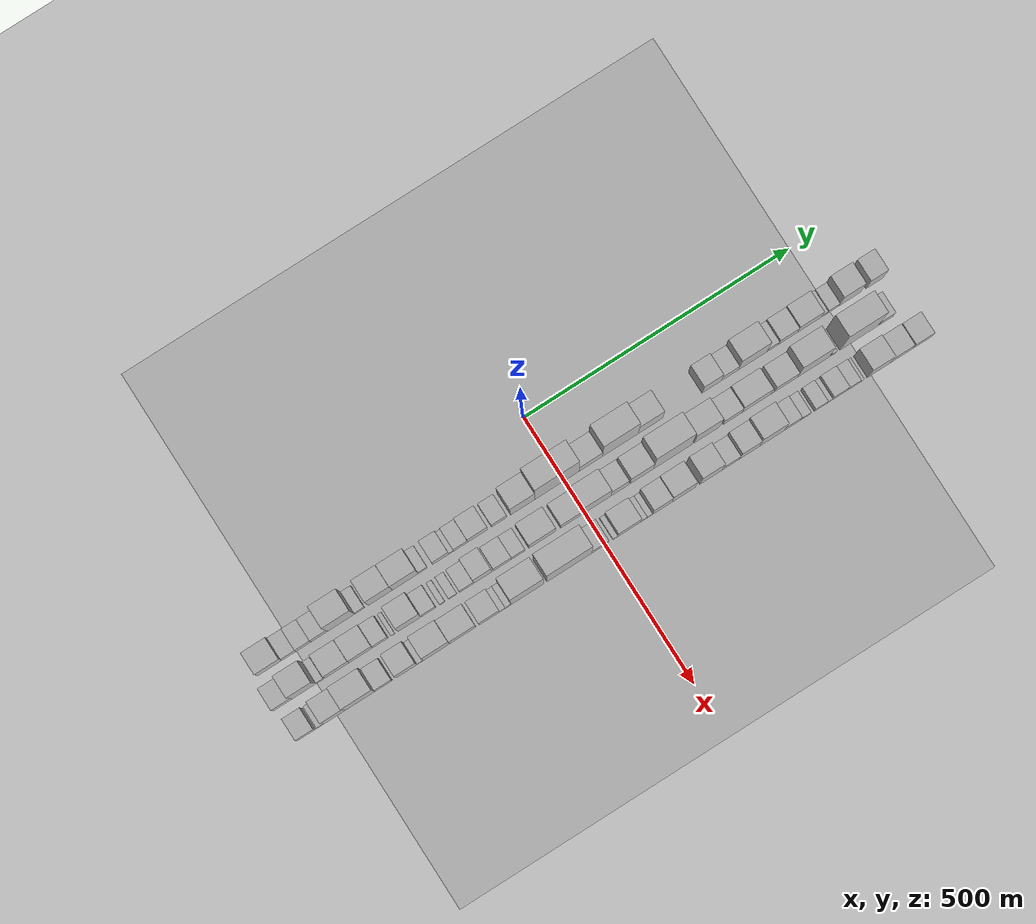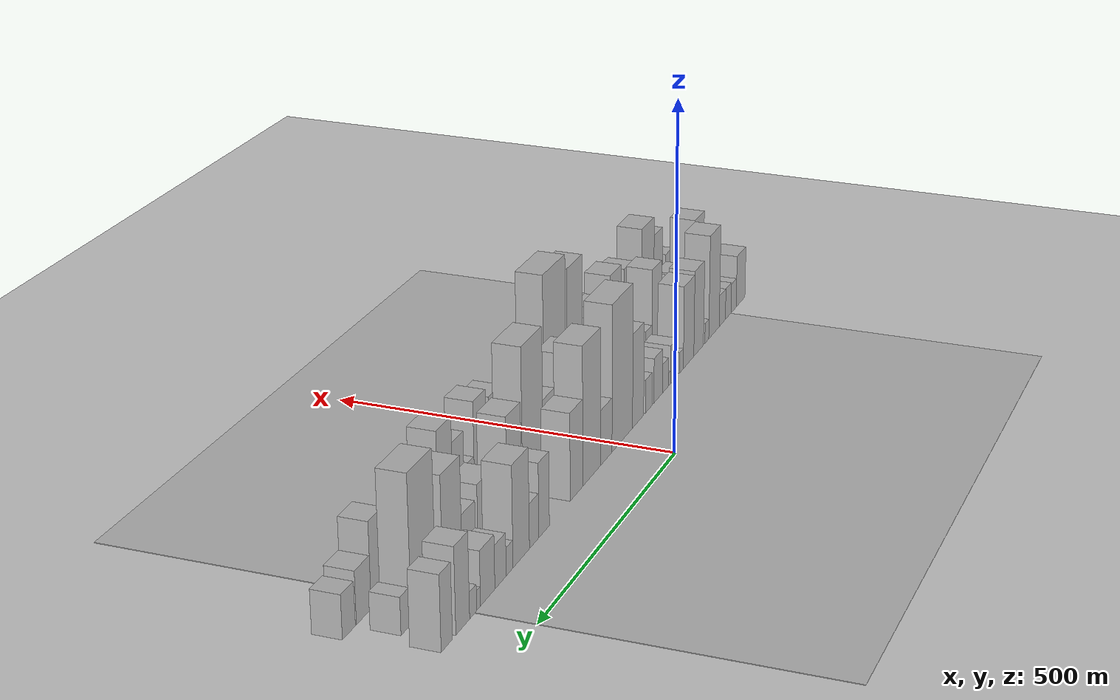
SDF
<?xml version="1.0" encoding="utf-8"?>

<sdf version="1.6">

   <world name="default">

      <gui fullscreen="0">

         <camera name="user_camera">

            <pose>-15 0 4.57585 0 0 0</pose>

            <view_controller>orbit</view_controller>

         </camera>

      </gui>

      <scene>

         <sky>

           <clouds>

             <speed>12</speed>

           </clouds>

         </sky>

         <ambient>0.4 0.4 0.4 1</ambient>

         <background>0.7 0.7 0.7 1</background>

         <shadows>1</shadows>

      </scene>

      <gravity>0 0 -9.8066</gravity>

      <magnetic_field>6e-06 2.3e-05 -4.2e-05</magnetic_field>

      <physics default="0" name="default_physics" type="ode">

         <ode>

            <solver>

               <type>quick</type>

               <iters>10</iters>

               <sor>1.0</sor>

               <use_dynamic_moi_rescaling>0</use_dynamic_moi_rescaling>

            </solver>

            <constraints>

               <cfm>0</cfm>

               <erp>0.2</erp>

               <contact_max_correcting_vel>100</contact_max_correcting_vel>

               <contact_surface_layer>0.001</contact_surface_layer>

            </constraints>

         </ode>

         <max_step_size>0.004</max_step_size>

         <real_time_factor>1</real_time_factor>

         <real_time_update_rate>250</real_time_update_rate>

      </physics>

      <light name="sun" type="directional">

         <cast_shadows>1</cast_shadows>

         <pose>0 0 10 0 0 0</pose>

         <diffuse>0.8 0.8 0.8 1</diffuse>

         <specular>0.2 0.2 0.2 1</specular>

         <attenuation>

            <range>1000</range>

            <constant>0.9</constant>

            <linear>0.01</linear>

            <quadratic>0.001</quadratic>

         </attenuation>

         <direction>-0.5 0.1 -0.9</direction>

      </light>

      <include>

         <name>ground_plane_1</name>

         <uri>model://HANNAS_ground_plane</uri>

         <pose>0 0 0  0 0 0</pose>

      </include>

      <include>

         <name>ground_plane_2</name>

         <uri>model://HANNAS_ground_plane</uri>

         <pose>100 0 0  0 0 0</pose>

      </include>

      <model name="building_1">

         <static>1</static>

         <pose frame="">100.0000 -548.4914 0 0.000000 0.000000 0.000000</pose>

         <link name="link">

            <pose frame="">0 0 42.00 0 0 0</pose>

            <collision name="collision">

               <geometry>

                  <box>

                     <size>40.0000 45.0173 84.0000</size>

                  </box>

               </geometry>

               <max_contacts>10</max_contacts>

               <surface>

                  <contact>

                     <ode/>

                  </contact>

                  <bounce/>

                  <friction>

                     <torsional>

                        <ode/>

                     </torsional>

                     <ode/>

                  </friction>

               </surface>

            </collision>

            <visual name="visual">

               <cast_shadows>0</cast_shadows>

               <geometry>

                  <box>

                     <size>40.0000 45.0173 84.0000</size>

                  </box>

               </geometry>

               <material>

                  <script>

                     <uri>model://HANNAS_wall/materials/scripts</uri>

                     <uri>model://HANNAS_wall/materials/textures</uri>

                     <name>vrc/HANNAS_wall</name>

                  </script>

               </material>

            </visual>

            <self_collide>0</self_collide>

            <enable_wind>0</enable_wind>

            <kinematic>0</kinematic>

         </link>

      </model>

      <model name="building_2">

         <static>1</static>

         <pose frame="">100.0000 -512.8878 0 0.000000 0.000000 0.000000</pose>

         <link name="link">

            <pose frame="">0 0 24.00 0 0 0</pose>

            <collision name="collision">

               <geometry>

                  <box>

                     <size>40.0000 26.1899 48.0000</size>

                  </box>

               </geometry>

               <max_contacts>10</max_contacts>

               <surface>

                  <contact>

                     <ode/>

                  </contact>

                  <bounce/>

                  <friction>

                     <torsional>

                        <ode/>

                     </torsional>

                     <ode/>

                  </friction>

               </surface>

            </collision>

            <visual name="visual">

               <cast_shadows>0</cast_shadows>

               <geometry>

                  <box>

                     <size>40.0000 26.1899 48.0000</size>

                  </box>

               </geometry>

               <material>

                  <script>

                     <uri>model://HANNAS_wall/materials/scripts</uri>

                     <uri>model://HANNAS_wall/materials/textures</uri>

                     <name>vrc/HANNAS_wall</name>

                  </script>

               </material>

            </visual>

            <self_collide>0</self_collide>

            <enable_wind>0</enable_wind>

            <kinematic>0</kinematic>

         </link>

      </model>

      <model name="building_3">

         <static>1</static>

         <pose frame="">100.0000 -485.8884 0 0.000000 0.000000 0.000000</pose>

         <link name="link">

            <pose frame="">0 0 25.50 0 0 0</pose>

            <collision name="collision">

               <geometry>

                  <box>

                     <size>40.0000 27.8088 51.0000</size>

                  </box>

               </geometry>

               <max_contacts>10</max_contacts>

               <surface>

                  <contact>

                     <ode/>

                  </contact>

                  <bounce/>

                  <friction>

                     <torsional>

                        <ode/>

                     </torsional>

                     <ode/>

                  </friction>

               </surface>

            </collision>

            <visual name="visual">

               <cast_shadows>0</cast_shadows>

               <geometry>

                  <box>

                     <size>40.0000 27.8088 51.0000</size>

                  </box>

               </geometry>

               <material>

                  <script>

                     <uri>model://HANNAS_wall/materials/scripts</uri>

                     <uri>model://HANNAS_wall/materials/textures</uri>

                     <name>vrc/HANNAS_wall</name>

                  </script>

               </material>

            </visual>

            <self_collide>0</self_collide>

            <enable_wind>0</enable_wind>

            <kinematic>0</kinematic>

         </link>

      </model>

      <model name="building_4">

         <static>1</static>

         <pose frame="">100.0000 -456.7219 0 0.000000 0.000000 0.000000</pose>

         <link name="link">

            <pose frame="">0 0 25.50 0 0 0</pose>

            <collision name="collision">

               <geometry>

                  <box>

                     <size>40.0000 30.5241 51.0000</size>

                  </box>

               </geometry>

               <max_contacts>10</max_contacts>

               <surface>

                  <contact>

                     <ode/>

                  </contact>

                  <bounce/>

                  <friction>

                     <torsional>

                        <ode/>

                     </torsional>

                     <ode/>

                  </friction>

               </surface>

            </collision>

            <visual name="visual">

               <cast_shadows>0</cast_shadows>

               <geometry>

                  <box>

                     <size>40.0000 30.5241 51.0000</size>

                  </box>

               </geometry>

               <material>

                  <script>

                     <uri>model://HANNAS_wall/materials/scripts</uri>

                     <uri>model://HANNAS_wall/materials/textures</uri>

                     <name>vrc/HANNAS_wall</name>

                  </script>

               </material>

            </visual>

            <self_collide>0</self_collide>

            <enable_wind>0</enable_wind>

            <kinematic>0</kinematic>

         </link>

      </model>

      <model name="building_5">

         <static>1</static>

         <pose frame="">100.0000 -416.1338 0 0.000000 0.000000 0.000000</pose>

         <link name="link">

            <pose frame="">0 0 82.50 0 0 0</pose>

            <collision name="collision">

               <geometry>

                  <box>

                     <size>40.0000 50.6523 165.0000</size>

                  </box>

               </geometry>

               <max_contacts>10</max_contacts>

               <surface>

                  <contact>

                     <ode/>

                  </contact>

                  <bounce/>

                  <friction>

                     <torsional>

                        <ode/>

                     </torsional>

                     <ode/>

                  </friction>

               </surface>

            </collision>

            <visual name="visual">

               <cast_shadows>0</cast_shadows>

               <geometry>

                  <box>

                     <size>40.0000 50.6523 165.0000</size>

                  </box>

               </geometry>

               <material>

                  <script>

                     <uri>model://HANNAS_wall/materials/scripts</uri>

                     <uri>model://HANNAS_wall/materials/textures</uri>

                     <name>vrc/HANNAS_wall</name>

                  </script>

               </material>

            </visual>

            <self_collide>0</self_collide>

            <enable_wind>0</enable_wind>

            <kinematic>0</kinematic>

         </link>

      </model>

      <model name="building_6">

         <static>1</static>

         <pose frame="">100.0000 -381.6510 0 0.000000 0.000000 0.000000</pose>

         <link name="link">

            <pose frame="">0 0 16.50 0 0 0</pose>

            <collision name="collision">

               <geometry>

                  <box>

                     <size>40.0000 18.3132 33.0000</size>

                  </box>

               </geometry>

               <max_contacts>10</max_contacts>

               <surface>

                  <contact>

                     <ode/>

                  </contact>

                  <bounce/>

                  <friction>

                     <torsional>

                        <ode/>

                     </torsional>

                     <ode/>

                  </friction>

               </surface>

            </collision>

            <visual name="visual">

               <cast_shadows>0</cast_shadows>

               <geometry>

                  <box>

                     <size>40.0000 18.3132 33.0000</size>

                  </box>

               </geometry>

               <material>

                  <script>

                     <uri>model://HANNAS_wall/materials/scripts</uri>

                     <uri>model://HANNAS_wall/materials/textures</uri>

                     <name>vrc/HANNAS_wall</name>

                  </script>

               </material>

            </visual>

            <self_collide>0</self_collide>

            <enable_wind>0</enable_wind>

            <kinematic>0</kinematic>

         </link>

      </model>

      <model name="building_7">

         <static>1</static>

         <pose frame="">100.0000 -343.0334 0 0.000000 0.000000 0.000000</pose>

         <link name="link">

            <pose frame="">0 0 67.50 0 0 0</pose>

            <collision name="collision">

               <geometry>

                  <box>

                     <size>40.0000 44.9220 135.0000</size>

                  </box>

               </geometry>

               <max_contacts>10</max_contacts>

               <surface>

                  <contact>

                     <ode/>

                  </contact>

                  <bounce/>

                  <friction>

                     <torsional>

                        <ode/>

                     </torsional>

                     <ode/>

                  </friction>

               </surface>

            </collision>

            <visual name="visual">

               <cast_shadows>0</cast_shadows>

               <geometry>

                  <box>

                     <size>40.0000 44.9220 135.0000</size>

                  </box>

               </geometry>

               <material>

                  <script>

                     <uri>model://HANNAS_wall/materials/scripts</uri>

                     <uri>model://HANNAS_wall/materials/textures</uri>

                     <name>vrc/HANNAS_wall</name>

                  </script>

               </material>

            </visual>

            <self_collide>0</self_collide>

            <enable_wind>0</enable_wind>

            <kinematic>0</kinematic>

         </link>

      </model>

      <model name="building_8">

         <static>1</static>

         <pose frame="">100.0000 -296.5302 0 0.000000 0.000000 0.000000</pose>

         <link name="link">

            <pose frame="">0 0 64.50 0 0 0</pose>

            <collision name="collision">

               <geometry>

                  <box>

                     <size>40.0000 48.0845 129.0000</size>

                  </box>

               </geometry>

               <max_contacts>10</max_contacts>

               <surface>

                  <contact>

                     <ode/>

                  </contact>

                  <bounce/>

                  <friction>

                     <torsional>

                        <ode/>

                     </torsional>

                     <ode/>

                  </friction>

               </surface>

            </collision>

            <visual name="visual">

               <cast_shadows>0</cast_shadows>

               <geometry>

                  <box>

                     <size>40.0000 48.0845 129.0000</size>

                  </box>

               </geometry>

               <material>

                  <script>

                     <uri>model://HANNAS_wall/materials/scripts</uri>

                     <uri>model://HANNAS_wall/materials/textures</uri>

                     <name>vrc/HANNAS_wall</name>

                  </script>

               </material>

            </visual>

            <self_collide>0</self_collide>

            <enable_wind>0</enable_wind>

            <kinematic>0</kinematic>

         </link>

      </model>

      <model name="building_9">

         <static>1</static>

         <pose frame="">100.0000 -264.0532 0 0.000000 0.000000 0.000000</pose>

         <link name="link">

            <pose frame="">0 0 16.50 0 0 0</pose>

            <collision name="collision">

               <geometry>

                  <box>

                     <size>40.0000 16.8695 33.0000</size>

                  </box>

               </geometry>

               <max_contacts>10</max_contacts>

               <surface>

                  <contact>

                     <ode/>

                  </contact>

                  <bounce/>

                  <friction>

                     <torsional>

                        <ode/>

                     </torsional>

                     <ode/>

                  </friction>

               </surface>

            </collision>

            <visual name="visual">

               <cast_shadows>0</cast_shadows>

               <geometry>

                  <box>

                     <size>40.0000 16.8695 33.0000</size>

                  </box>

               </geometry>

               <material>

                  <script>

                     <uri>model://HANNAS_wall/materials/scripts</uri>

                     <uri>model://HANNAS_wall/materials/textures</uri>

                     <name>vrc/HANNAS_wall</name>

                  </script>

               </material>

            </visual>

            <self_collide>0</self_collide>

            <enable_wind>0</enable_wind>

            <kinematic>0</kinematic>

         </link>

      </model>

      <model name="building_10">

         <static>1</static>

         <pose frame="">100.0000 -230.4806 0 0.000000 0.000000 0.000000</pose>

         <link name="link">

            <pose frame="">0 0 30.00 0 0 0</pose>

            <collision name="collision">

               <geometry>

                  <box>

                     <size>40.0000 30.2757 60.0000</size>

                  </box>

               </geometry>

               <max_contacts>10</max_contacts>

               <surface>

                  <contact>

                     <ode/>

                  </contact>

                  <bounce/>

                  <friction>

                     <torsional>

                        <ode/>

                     </torsional>

                     <ode/>

                  </friction>

               </surface>

            </collision>

            <visual name="visual">

               <cast_shadows>0</cast_shadows>

               <geometry>

                  <box>

                     <size>40.0000 30.2757 60.0000</size>

                  </box>

               </geometry>

               <material>

                  <script>

                     <uri>model://HANNAS_wall/materials/scripts</uri>

                     <uri>model://HANNAS_wall/materials/textures</uri>

                     <name>vrc/HANNAS_wall</name>

                  </script>

               </material>

            </visual>

            <self_collide>0</self_collide>

            <enable_wind>0</enable_wind>

            <kinematic>0</kinematic>

         </link>

      </model>

      <model name="building_11">

         <static>1</static>

         <pose frame="">100.0000 -211.0140 0 0.000000 0.000000 0.000000</pose>

         <link name="link">

            <pose frame="">0 0 10.50 0 0 0</pose>

            <collision name="collision">

               <geometry>

                  <box>

                     <size>40.0000 8.6574 21.0000</size>

                  </box>

               </geometry>

               <max_contacts>10</max_contacts>

               <surface>

                  <contact>

                     <ode/>

                  </contact>

                  <bounce/>

                  <friction>

                     <torsional>

                        <ode/>

                     </torsional>

                     <ode/>

                  </friction>

               </surface>

            </collision>

            <visual name="visual">

               <cast_shadows>0</cast_shadows>

               <geometry>

                  <box>

                     <size>40.0000 8.6574 21.0000</size>

                  </box>

               </geometry>

               <material>

                  <script>

                     <uri>model://HANNAS_wall/materials/scripts</uri>

                     <uri>model://HANNAS_wall/materials/textures</uri>

                     <name>vrc/HANNAS_wall</name>

                  </script>

               </material>

            </visual>

            <self_collide>0</self_collide>

            <enable_wind>0</enable_wind>

            <kinematic>0</kinematic>

         </link>

      </model>

      <model name="building_12">

         <static>1</static>

         <pose frame="">100.0000 -193.4829 0 0.000000 0.000000 0.000000</pose>

         <link name="link">

            <pose frame="">0 0 22.50 0 0 0</pose>

            <collision name="collision">

               <geometry>

                  <box>

                     <size>40.0000 26.4049 45.0000</size>

                  </box>

               </geometry>

               <max_contacts>10</max_contacts>

               <surface>

                  <contact>

                     <ode/>

                  </contact>

                  <bounce/>

                  <friction>

                     <torsional>

                        <ode/>

                     </torsional>

                     <ode/>

                  </friction>

               </surface>

            </collision>

            <visual name="visual">

               <cast_shadows>0</cast_shadows>

               <geometry>

                  <box>

                     <size>40.0000 26.4049 45.0000</size>

                  </box>

               </geometry>

               <material>

                  <script>

                     <uri>model://HANNAS_wall/materials/scripts</uri>

                     <uri>model://HANNAS_wall/materials/textures</uri>

                     <name>vrc/HANNAS_wall</name>

                  </script>

               </material>

            </visual>

            <self_collide>0</self_collide>

            <enable_wind>0</enable_wind>

            <kinematic>0</kinematic>

         </link>

      </model>

      <model name="building_13">

         <static>1</static>

         <pose frame="">100.0000 -161.5967 0 0.000000 0.000000 0.000000</pose>

         <link name="link">

            <pose frame="">0 0 34.50 0 0 0</pose>

            <collision name="collision">

               <geometry>

                  <box>

                     <size>40.0000 37.3676 69.0000</size>

                  </box>

               </geometry>

               <max_contacts>10</max_contacts>

               <surface>

                  <contact>

                     <ode/>

                  </contact>

                  <bounce/>

                  <friction>

                     <torsional>

                        <ode/>

                     </torsional>

                     <ode/>

                  </friction>

               </surface>

            </collision>

            <visual name="visual">

               <cast_shadows>0</cast_shadows>

               <geometry>

                  <box>

                     <size>40.0000 37.3676 69.0000</size>

                  </box>

               </geometry>

               <material>

                  <script>

                     <uri>model://HANNAS_wall/materials/scripts</uri>

                     <uri>model://HANNAS_wall/materials/textures</uri>

                     <name>vrc/HANNAS_wall</name>

                  </script>

               </material>

            </visual>

            <self_collide>0</self_collide>

            <enable_wind>0</enable_wind>

            <kinematic>0</kinematic>

         </link>

      </model>

      <model name="building_14">

         <static>1</static>

         <pose frame="">100.0000 -121.5014 0 0.000000 0.000000 0.000000</pose>

         <link name="link">

            <pose frame="">0 0 25.50 0 0 0</pose>

            <collision name="collision">

               <geometry>

                  <box>

                     <size>40.0000 28.8231 51.0000</size>

                  </box>

               </geometry>

               <max_contacts>10</max_contacts>

               <surface>

                  <contact>

                     <ode/>

                  </contact>

                  <bounce/>

                  <friction>

                     <torsional>

                        <ode/>

                     </torsional>

                     <ode/>

                  </friction>

               </surface>

            </collision>

            <visual name="visual">

               <cast_shadows>0</cast_shadows>

               <geometry>

                  <box>

                     <size>40.0000 28.8231 51.0000</size>

                  </box>

               </geometry>

               <material>

                  <script>

                     <uri>model://HANNAS_wall/materials/scripts</uri>

                     <uri>model://HANNAS_wall/materials/textures</uri>

                     <name>vrc/HANNAS_wall</name>

                  </script>

               </material>

            </visual>

            <self_collide>0</self_collide>

            <enable_wind>0</enable_wind>

            <kinematic>0</kinematic>

         </link>

      </model>

      <model name="building_15">

         <static>1</static>

         <pose frame="">100.0000 -77.2038 0 0.000000 0.000000 0.000000</pose>

         <link name="link">

            <pose frame="">0 0 70.50 0 0 0</pose>

            <collision name="collision">

               <geometry>

                  <box>

                     <size>40.0000 45.7720 141.0000</size>

                  </box>

               </geometry>

               <max_contacts>10</max_contacts>

               <surface>

                  <contact>

                     <ode/>

                  </contact>

                  <bounce/>

                  <friction>

                     <torsional>

                        <ode/>

                     </torsional>

                     <ode/>

                  </friction>

               </surface>

            </collision>

            <visual name="visual">

               <cast_shadows>0</cast_shadows>

               <geometry>

                  <box>

                     <size>40.0000 45.7720 141.0000</size>

                  </box>

               </geometry>

               <material>

                  <script>

                     <uri>model://HANNAS_wall/materials/scripts</uri>

                     <uri>model://HANNAS_wall/materials/textures</uri>

                     <name>vrc/HANNAS_wall</name>

                  </script>

               </material>

            </visual>

            <self_collide>0</self_collide>

            <enable_wind>0</enable_wind>

            <kinematic>0</kinematic>

         </link>

      </model>

      <model name="building_16">

         <static>1</static>

         <pose frame="">100.0000 -13.2444 0 0.000000 0.000000 0.000000</pose>

         <link name="link">

            <pose frame="">0 0 108.00 0 0 0</pose>

            <collision name="collision">

               <geometry>

                  <box>

                     <size>40.0000 82.1468 216.0000</size>

                  </box>

               </geometry>

               <max_contacts>10</max_contacts>

               <surface>

                  <contact>

                     <ode/>

                  </contact>

                  <bounce/>

                  <friction>

                     <torsional>

                        <ode/>

                     </torsional>

                     <ode/>

                  </friction>

               </surface>

            </collision>

            <visual name="visual">

               <cast_shadows>0</cast_shadows>

               <geometry>

                  <box>

                     <size>40.0000 82.1468 216.0000</size>

                  </box>

               </geometry>

               <material>

                  <script>

                     <uri>model://HANNAS_wall/materials/scripts</uri>

                     <uri>model://HANNAS_wall/materials/textures</uri>

                     <name>vrc/HANNAS_wall</name>

                  </script>

               </material>

            </visual>

            <self_collide>0</self_collide>

            <enable_wind>0</enable_wind>

            <kinematic>0</kinematic>

         </link>

      </model>

      <model name="building_17">

         <static>1</static>

         <pose frame="">100.0000 49.7188 0 0.000000 0.000000 0.000000</pose>

         <link name="link">

            <pose frame="">0 0 40.50 0 0 0</pose>

            <collision name="collision">

               <geometry>

                  <box>

                     <size>40.0000 43.7797 81.0000</size>

                  </box>

               </geometry>

               <max_contacts>10</max_contacts>

               <surface>

                  <contact>

                     <ode/>

                  </contact>

                  <bounce/>

                  <friction>

                     <torsional>

                        <ode/>

                     </torsional>

                     <ode/>

                  </friction>

               </surface>

            </collision>

            <visual name="visual">

               <cast_shadows>0</cast_shadows>

               <geometry>

                  <box>

                     <size>40.0000 43.7797 81.0000</size>

                  </box>

               </geometry>

               <material>

                  <script>

                     <uri>model://HANNAS_wall/materials/scripts</uri>

                     <uri>model://HANNAS_wall/materials/textures</uri>

                     <name>vrc/HANNAS_wall</name>

                  </script>

               </material>

            </visual>

            <self_collide>0</self_collide>

            <enable_wind>0</enable_wind>

            <kinematic>0</kinematic>

         </link>

      </model>

      <model name="building_18">

         <static>1</static>

         <pose frame="">100.0000 105.1265 0 0.000000 0.000000 0.000000</pose>

         <link name="link">

            <pose frame="">0 0 100.50 0 0 0</pose>

            <collision name="collision">

               <geometry>

                  <box>

                     <size>40.0000 67.0357 201.0000</size>

                  </box>

               </geometry>

               <max_contacts>10</max_contacts>

               <surface>

                  <contact>

                     <ode/>

                  </contact>

                  <bounce/>

                  <friction>

                     <torsional>

                        <ode/>

                     </torsional>

                     <ode/>

                  </friction>

               </surface>

            </collision>

            <visual name="visual">

               <cast_shadows>0</cast_shadows>

               <geometry>

                  <box>

                     <size>40.0000 67.0357 201.0000</size>

                  </box>

               </geometry>

               <material>

                  <script>

                     <uri>model://HANNAS_wall/materials/scripts</uri>

                     <uri>model://HANNAS_wall/materials/textures</uri>

                     <name>vrc/HANNAS_wall</name>

                  </script>

               </material>

            </visual>

            <self_collide>0</self_collide>

            <enable_wind>0</enable_wind>

            <kinematic>0</kinematic>

         </link>

      </model>

      <model name="building_19">

         <static>1</static>

         <pose frame="">100.0000 161.7605 0 0.000000 0.000000 0.000000</pose>

         <link name="link">

            <pose frame="">0 0 63.00 0 0 0</pose>

            <collision name="collision">

               <geometry>

                  <box>

                     <size>40.0000 46.2322 126.0000</size>

                  </box>

               </geometry>

               <max_contacts>10</max_contacts>

               <surface>

                  <contact>

                     <ode/>

                  </contact>

                  <bounce/>

                  <friction>

                     <torsional>

                        <ode/>

                     </torsional>

                     <ode/>

                  </friction>

               </surface>

            </collision>

            <visual name="visual">

               <cast_shadows>0</cast_shadows>

               <geometry>

                  <box>

                     <size>40.0000 46.2322 126.0000</size>

                  </box>

               </geometry>

               <material>

                  <script>

                     <uri>model://HANNAS_wall/materials/scripts</uri>

                     <uri>model://HANNAS_wall/materials/textures</uri>

                     <name>vrc/HANNAS_wall</name>

                  </script>

               </material>

            </visual>

            <self_collide>0</self_collide>

            <enable_wind>0</enable_wind>

            <kinematic>0</kinematic>

         </link>

      </model>

      <model name="building_20">

         <static>1</static>

         <pose frame="">100.0000 276.7857 0 0.000000 0.000000 0.000000</pose>

         <link name="link">

            <pose frame="">0 0 52.50 0 0 0</pose>

            <collision name="collision">

               <geometry>

                  <box>

                     <size>40.0000 35.9394 105.0000</size>

                  </box>

               </geometry>

               <max_contacts>10</max_contacts>

               <surface>

                  <contact>

                     <ode/>

                  </contact>

                  <bounce/>

                  <friction>

                     <torsional>

                        <ode/>

                     </torsional>

                     <ode/>

                  </friction>

               </surface>

            </collision>

            <visual name="visual">

               <cast_shadows>0</cast_shadows>

               <geometry>

                  <box>

                     <size>40.0000 35.9394 105.0000</size>

                  </box>

               </geometry>

               <material>

                  <script>

                     <uri>model://HANNAS_wall/materials/scripts</uri>

                     <uri>model://HANNAS_wall/materials/textures</uri>

                     <name>vrc/HANNAS_wall</name>

                  </script>

               </material>

            </visual>

            <self_collide>0</self_collide>

            <enable_wind>0</enable_wind>

            <kinematic>0</kinematic>

         </link>

      </model>

      <model name="building_21">

         <static>1</static>

         <pose frame="">100.0000 310.7436 0 0.000000 0.000000 0.000000</pose>

         <link name="link">

            <pose frame="">0 0 31.50 0 0 0</pose>

            <collision name="collision">

               <geometry>

                  <box>

                     <size>40.0000 31.9765 63.0000</size>

                  </box>

               </geometry>

               <max_contacts>10</max_contacts>

               <surface>

                  <contact>

                     <ode/>

                  </contact>

                  <bounce/>

                  <friction>

                     <torsional>

                        <ode/>

                     </torsional>

                     <ode/>

                  </friction>

               </surface>

            </collision>

            <visual name="visual">

               <cast_shadows>0</cast_shadows>

               <geometry>

                  <box>

                     <size>40.0000 31.9765 63.0000</size>

                  </box>

               </geometry>

               <material>

                  <script>

                     <uri>model://HANNAS_wall/materials/scripts</uri>

                     <uri>model://HANNAS_wall/materials/textures</uri>

                     <name>vrc/HANNAS_wall</name>

                  </script>

               </material>

            </visual>

            <self_collide>0</self_collide>

            <enable_wind>0</enable_wind>

            <kinematic>0</kinematic>

         </link>

      </model>

      <model name="building_22">

         <static>1</static>

         <pose frame="">100.0000 353.7843 0 0.000000 0.000000 0.000000</pose>

         <link name="link">

            <pose frame="">0 0 70.50 0 0 0</pose>

            <collision name="collision">

               <geometry>

                  <box>

                     <size>40.0000 54.1048 141.0000</size>

                  </box>

               </geometry>

               <max_contacts>10</max_contacts>

               <surface>

                  <contact>

                     <ode/>

                  </contact>

                  <bounce/>

                  <friction>

                     <torsional>

                        <ode/>

                     </torsional>

                     <ode/>

                  </friction>

               </surface>

            </collision>

            <visual name="visual">

               <cast_shadows>0</cast_shadows>

               <geometry>

                  <box>

                     <size>40.0000 54.1048 141.0000</size>

                  </box>

               </geometry>

               <material>

                  <script>

                     <uri>model://HANNAS_wall/materials/scripts</uri>

                     <uri>model://HANNAS_wall/materials/textures</uri>

                     <name>vrc/HANNAS_wall</name>

                  </script>

               </material>

            </visual>

            <self_collide>0</self_collide>

            <enable_wind>0</enable_wind>

            <kinematic>0</kinematic>

         </link>

      </model>

      <model name="building_23">

         <static>1</static>

         <pose frame="">100.0000 391.8580 0 0.000000 0.000000 0.000000</pose>

         <link name="link">

            <pose frame="">0 0 19.50 0 0 0</pose>

            <collision name="collision">

               <geometry>

                  <box>

                     <size>40.0000 22.0427 39.0000</size>

                  </box>

               </geometry>

               <max_contacts>10</max_contacts>

               <surface>

                  <contact>

                     <ode/>

                  </contact>

                  <bounce/>

                  <friction>

                     <torsional>

                        <ode/>

                     </torsional>

                     <ode/>

                  </friction>

               </surface>

            </collision>

            <visual name="visual">

               <cast_shadows>0</cast_shadows>

               <geometry>

                  <box>

                     <size>40.0000 22.0427 39.0000</size>

                  </box>

               </geometry>

               <material>

                  <script>

                     <uri>model://HANNAS_wall/materials/scripts</uri>

                     <uri>model://HANNAS_wall/materials/textures</uri>

                     <name>vrc/HANNAS_wall</name>

                  </script>

               </material>

            </visual>

            <self_collide>0</self_collide>

            <enable_wind>0</enable_wind>

            <kinematic>0</kinematic>

         </link>

      </model>

      <model name="building_24">

         <static>1</static>

         <pose frame="">100.0000 420.8539 0 0.000000 0.000000 0.000000</pose>

         <link name="link">

            <pose frame="">0 0 30.00 0 0 0</pose>

            <collision name="collision">

               <geometry>

                  <box>

                     <size>40.0000 35.9491 60.0000</size>

                  </box>

               </geometry>

               <max_contacts>10</max_contacts>

               <surface>

                  <contact>

                     <ode/>

                  </contact>

                  <bounce/>

                  <friction>

                     <torsional>

                        <ode/>

                     </torsional>

                     <ode/>

                  </friction>

               </surface>

            </collision>

            <visual name="visual">

               <cast_shadows>0</cast_shadows>

               <geometry>

                  <box>

                     <size>40.0000 35.9491 60.0000</size>

                  </box>

               </geometry>

               <material>

                  <script>

                     <uri>model://HANNAS_wall/materials/scripts</uri>

                     <uri>model://HANNAS_wall/materials/textures</uri>

                     <name>vrc/HANNAS_wall</name>

                  </script>

               </material>

            </visual>

            <self_collide>0</self_collide>

            <enable_wind>0</enable_wind>

            <kinematic>0</kinematic>

         </link>

      </model>

      <model name="building_25">

         <static>1</static>

         <pose frame="">100.0000 461.1783 0 0.000000 0.000000 0.000000</pose>

         <link name="link">

            <pose frame="">0 0 37.50 0 0 0</pose>

            <collision name="collision">

               <geometry>

                  <box>

                     <size>40.0000 44.6996 75.0000</size>

                  </box>

               </geometry>

               <max_contacts>10</max_contacts>

               <surface>

                  <contact>

                     <ode/>

                  </contact>

                  <bounce/>

                  <friction>

                     <torsional>

                        <ode/>

                     </torsional>

                     <ode/>

                  </friction>

               </surface>

            </collision>

            <visual name="visual">

               <cast_shadows>0</cast_shadows>

               <geometry>

                  <box>

                     <size>40.0000 44.6996 75.0000</size>

                  </box>

               </geometry>

               <material>

                  <script>

                     <uri>model://HANNAS_wall/materials/scripts</uri>

                     <uri>model://HANNAS_wall/materials/textures</uri>

                     <name>vrc/HANNAS_wall</name>

                  </script>

               </material>

            </visual>

            <self_collide>0</self_collide>

            <enable_wind>0</enable_wind>

            <kinematic>0</kinematic>

         </link>

      </model>

      <model name="building_26">

         <static>1</static>

         <pose frame="">100.0000 489.3432 0 0.000000 0.000000 0.000000</pose>

         <link name="link">

            <pose frame="">0 0 13.50 0 0 0</pose>

            <collision name="collision">

               <geometry>

                  <box>

                     <size>40.0000 11.6302 27.0000</size>

                  </box>

               </geometry>

               <max_contacts>10</max_contacts>

               <surface>

                  <contact>

                     <ode/>

                  </contact>

                  <bounce/>

                  <friction>

                     <torsional>

                        <ode/>

                     </torsional>

                     <ode/>

                  </friction>

               </surface>

            </collision>

            <visual name="visual">

               <cast_shadows>0</cast_shadows>

               <geometry>

                  <box>

                     <size>40.0000 11.6302 27.0000</size>

                  </box>

               </geometry>

               <material>

                  <script>

                     <uri>model://HANNAS_wall/materials/scripts</uri>

                     <uri>model://HANNAS_wall/materials/textures</uri>

                     <name>vrc/HANNAS_wall</name>

                  </script>

               </material>

            </visual>

            <self_collide>0</self_collide>

            <enable_wind>0</enable_wind>

            <kinematic>0</kinematic>

         </link>

      </model>

      <model name="building_27">

         <static>1</static>

         <pose frame="">100.0000 505.8549 0 0.000000 0.000000 0.000000</pose>

         <link name="link">

            <pose frame="">0 0 18.00 0 0 0</pose>

            <collision name="collision">

               <geometry>

                  <box>

                     <size>40.0000 21.3932 36.0000</size>

                  </box>

               </geometry>

               <max_contacts>10</max_contacts>

               <surface>

                  <contact>

                     <ode/>

                  </contact>

                  <bounce/>

                  <friction>

                     <torsional>

                        <ode/>

                     </torsional>

                     <ode/>

                  </friction>

               </surface>

            </collision>

            <visual name="visual">

               <cast_shadows>0</cast_shadows>

               <geometry>

                  <box>

                     <size>40.0000 21.3932 36.0000</size>

                  </box>

               </geometry>

               <material>

                  <script>

                     <uri>model://HANNAS_wall/materials/scripts</uri>

                     <uri>model://HANNAS_wall/materials/textures</uri>

                     <name>vrc/HANNAS_wall</name>

                  </script>

               </material>

            </visual>

            <self_collide>0</self_collide>

            <enable_wind>0</enable_wind>

            <kinematic>0</kinematic>

         </link>

      </model>

      <model name="building_28">

         <static>1</static>

         <pose frame="">100.0000 537.0543 0 0.000000 0.000000 0.000000</pose>

         <link name="link">

            <pose frame="">0 0 58.50 0 0 0</pose>

            <collision name="collision">

               <geometry>

                  <box>

                     <size>40.0000 41.0055 117.0000</size>

                  </box>

               </geometry>

               <max_contacts>10</max_contacts>

               <surface>

                  <contact>

                     <ode/>

                  </contact>

                  <bounce/>

                  <friction>

                     <torsional>

                        <ode/>

                     </torsional>

                     <ode/>

                  </friction>

               </surface>

            </collision>

            <visual name="visual">

               <cast_shadows>0</cast_shadows>

               <geometry>

                  <box>

                     <size>40.0000 41.0055 117.0000</size>

                  </box>

               </geometry>

               <material>

                  <script>

                     <uri>model://HANNAS_wall/materials/scripts</uri>

                     <uri>model://HANNAS_wall/materials/textures</uri>

                     <name>vrc/HANNAS_wall</name>

                  </script>

               </material>

            </visual>

            <self_collide>0</self_collide>

            <enable_wind>0</enable_wind>

            <kinematic>0</kinematic>

         </link>

      </model>

      <model name="building_29">

         <static>1</static>

         <pose frame="">100.0000 583.9292 0 0.000000 0.000000 0.000000</pose>

         <link name="link">

            <pose frame="">0 0 51.00 0 0 0</pose>

            <collision name="collision">

               <geometry>

                  <box>

                     <size>40.0000 32.7443 102.0000</size>

                  </box>

               </geometry>

               <max_contacts>10</max_contacts>

               <surface>

                  <contact>

                     <ode/>

                  </contact>

                  <bounce/>

                  <friction>

                     <torsional>

                        <ode/>

                     </torsional>

                     <ode/>

                  </friction>

               </surface>

            </collision>

            <visual name="visual">

               <cast_shadows>0</cast_shadows>

               <geometry>

                  <box>

                     <size>40.0000 32.7443 102.0000</size>

                  </box>

               </geometry>

               <material>

                  <script>

                     <uri>model://HANNAS_wall/materials/scripts</uri>

                     <uri>model://HANNAS_wall/materials/textures</uri>

                     <name>vrc/HANNAS_wall</name>

                  </script>

               </material>

            </visual>

            <self_collide>0</self_collide>

            <enable_wind>0</enable_wind>

            <kinematic>0</kinematic>

         </link>

      </model>

      <model name="building_30">

         <static>1</static>

         <pose frame="">160.0000 -562.5700 0 0.000000 0.000000 0.000000</pose>

         <link name="link">

            <pose frame="">0 0 31.50 0 0 0</pose>

            <collision name="collision">

               <geometry>

                  <box>

                     <size>40.0000 34.8599 63.0000</size>

                  </box>

               </geometry>

               <max_contacts>10</max_contacts>

               <surface>

                  <contact>

                     <ode/>

                  </contact>

                  <bounce/>

                  <friction>

                     <torsional>

                        <ode/>

                     </torsional>

                     <ode/>

                  </friction>

               </surface>

            </collision>

            <visual name="visual">

               <cast_shadows>0</cast_shadows>

               <geometry>

                  <box>

                     <size>40.0000 34.8599 63.0000</size>

                  </box>

               </geometry>

               <material>

                  <script>

                     <uri>model://HANNAS_wall/materials/scripts</uri>

                     <uri>model://HANNAS_wall/materials/textures</uri>

                     <name>vrc/HANNAS_wall</name>

                  </script>

               </material>

            </visual>

            <self_collide>0</self_collide>

            <enable_wind>0</enable_wind>

            <kinematic>0</kinematic>

         </link>

      </model>

      <model name="building_31">

         <static>1</static>

         <pose frame="">160.0000 -522.5923 0 0.000000 0.000000 0.000000</pose>

         <link name="link">

            <pose frame="">0 0 72.00 0 0 0</pose>

            <collision name="collision">

               <geometry>

                  <box>

                     <size>40.0000 45.0955 144.0000</size>

                  </box>

               </geometry>

               <max_contacts>10</max_contacts>

               <surface>

                  <contact>

                     <ode/>

                  </contact>

                  <bounce/>

                  <friction>

                     <torsional>

                        <ode/>

                     </torsional>

                     <ode/>

                  </friction>

               </surface>

            </collision>

            <visual name="visual">

               <cast_shadows>0</cast_shadows>

               <geometry>

                  <box>

                     <size>40.0000 45.0955 144.0000</size>

                  </box>

               </geometry>

               <material>

                  <script>

                     <uri>model://HANNAS_wall/materials/scripts</uri>

                     <uri>model://HANNAS_wall/materials/textures</uri>

                     <name>vrc/HANNAS_wall</name>

                  </script>

               </material>

            </visual>

            <self_collide>0</self_collide>

            <enable_wind>0</enable_wind>

            <kinematic>0</kinematic>

         </link>

      </model>

      <model name="building_32">

         <static>1</static>

         <pose frame="">160.0000 -493.3652 0 0.000000 0.000000 0.000000</pose>

         <link name="link">

            <pose frame="">0 0 13.50 0 0 0</pose>

            <collision name="collision">

               <geometry>

                  <box>

                     <size>40.0000 13.3587 27.0000</size>

                  </box>

               </geometry>

               <max_contacts>10</max_contacts>

               <surface>

                  <contact>

                     <ode/>

                  </contact>

                  <bounce/>

                  <friction>

                     <torsional>

                        <ode/>

                     </torsional>

                     <ode/>

                  </friction>

               </surface>

            </collision>

            <visual name="visual">

               <cast_shadows>0</cast_shadows>

               <geometry>

                  <box>

                     <size>40.0000 13.3587 27.0000</size>

                  </box>

               </geometry>

               <material>

                  <script>

                     <uri>model://HANNAS_wall/materials/scripts</uri>

                     <uri>model://HANNAS_wall/materials/textures</uri>

                     <name>vrc/HANNAS_wall</name>

                  </script>

               </material>

            </visual>

            <self_collide>0</self_collide>

            <enable_wind>0</enable_wind>

            <kinematic>0</kinematic>

         </link>

      </model>

      <model name="building_33">

         <static>1</static>

         <pose frame="">160.0000 -461.1249 0 0.000000 0.000000 0.000000</pose>

         <link name="link">

            <pose frame="">0 0 39.00 0 0 0</pose>

            <collision name="collision">

               <geometry>

                  <box>

                     <size>40.0000 45.1219 78.0000</size>

                  </box>

               </geometry>

               <max_contacts>10</max_contacts>

               <surface>

                  <contact>

                     <ode/>

                  </contact>

                  <bounce/>

                  <friction>

                     <torsional>

                        <ode/>

                     </torsional>

                     <ode/>

                  </friction>

               </surface>

            </collision>

            <visual name="visual">

               <cast_shadows>0</cast_shadows>

               <geometry>

                  <box>

                     <size>40.0000 45.1219 78.0000</size>

                  </box>

               </geometry>

               <material>

                  <script>

                     <uri>model://HANNAS_wall/materials/scripts</uri>

                     <uri>model://HANNAS_wall/materials/textures</uri>

                     <name>vrc/HANNAS_wall</name>

                  </script>

               </material>

            </visual>

            <self_collide>0</self_collide>

            <enable_wind>0</enable_wind>

            <kinematic>0</kinematic>

         </link>

      </model>

      <model name="building_34">

         <static>1</static>

         <pose frame="">160.0000 -416.7266 0 0.000000 0.000000 0.000000</pose>

         <link name="link">

            <pose frame="">0 0 37.50 0 0 0</pose>

            <collision name="collision">

               <geometry>

                  <box>

                     <size>40.0000 43.6748 75.0000</size>

                  </box>

               </geometry>

               <max_contacts>10</max_contacts>

               <surface>

                  <contact>

                     <ode/>

                  </contact>

                  <bounce/>

                  <friction>

                     <torsional>

                        <ode/>

                     </torsional>

                     <ode/>

                  </friction>

               </surface>

            </collision>

            <visual name="visual">

               <cast_shadows>0</cast_shadows>

               <geometry>

                  <box>

                     <size>40.0000 43.6748 75.0000</size>

                  </box>

               </geometry>

               <material>

                  <script>

                     <uri>model://HANNAS_wall/materials/scripts</uri>

                     <uri>model://HANNAS_wall/materials/textures</uri>

                     <name>vrc/HANNAS_wall</name>

                  </script>

               </material>

            </visual>

            <self_collide>0</self_collide>

            <enable_wind>0</enable_wind>

            <kinematic>0</kinematic>

         </link>

      </model>

      <model name="building_35">

         <static>1</static>

         <pose frame="">160.0000 -380.7941 0 0.000000 0.000000 0.000000</pose>

         <link name="link">

            <pose frame="">0 0 27.00 0 0 0</pose>

            <collision name="collision">

               <geometry>

                  <box>

                     <size>40.0000 28.1901 54.0000</size>

                  </box>

               </geometry>

               <max_contacts>10</max_contacts>

               <surface>

                  <contact>

                     <ode/>

                  </contact>

                  <bounce/>

                  <friction>

                     <torsional>

                        <ode/>

                     </torsional>

                     <ode/>

                  </friction>

               </surface>

            </collision>

            <visual name="visual">

               <cast_shadows>0</cast_shadows>

               <geometry>

                  <box>

                     <size>40.0000 28.1901 54.0000</size>

                  </box>

               </geometry>

               <material>

                  <script>

                     <uri>model://HANNAS_wall/materials/scripts</uri>

                     <uri>model://HANNAS_wall/materials/textures</uri>

                     <name>vrc/HANNAS_wall</name>

                  </script>

               </material>

            </visual>

            <self_collide>0</self_collide>

            <enable_wind>0</enable_wind>

            <kinematic>0</kinematic>

         </link>

      </model>

      <model name="building_36">

         <static>1</static>

         <pose frame="">160.0000 -358.0864 0 0.000000 0.000000 0.000000</pose>

         <link name="link">

            <pose frame="">0 0 7.50 0 0 0</pose>

            <collision name="collision">

               <geometry>

                  <box>

                     <size>40.0000 7.2253 15.0000</size>

                  </box>

               </geometry>

               <max_contacts>10</max_contacts>

               <surface>

                  <contact>

                     <ode/>

                  </contact>

                  <bounce/>

                  <friction>

                     <torsional>

                        <ode/>

                     </torsional>

                     <ode/>

                  </friction>

               </surface>

            </collision>

            <visual name="visual">

               <cast_shadows>0</cast_shadows>

               <geometry>

                  <box>

                     <size>40.0000 7.2253 15.0000</size>

                  </box>

               </geometry>

               <material>

                  <script>

                     <uri>model://HANNAS_wall/materials/scripts</uri>

                     <uri>model://HANNAS_wall/materials/textures</uri>

                     <name>vrc/HANNAS_wall</name>

                  </script>

               </material>

            </visual>

            <self_collide>0</self_collide>

            <enable_wind>0</enable_wind>

            <kinematic>0</kinematic>

         </link>

      </model>

      <model name="building_37">

         <static>1</static>

         <pose frame="">160.0000 -326.3015 0 0.000000 0.000000 0.000000</pose>

         <link name="link">

            <pose frame="">0 0 67.50 0 0 0</pose>

            <collision name="collision">

               <geometry>

                  <box>

                     <size>40.0000 42.3445 135.0000</size>

                  </box>

               </geometry>

               <max_contacts>10</max_contacts>

               <surface>

                  <contact>

                     <ode/>

                  </contact>

                  <bounce/>

                  <friction>

                     <torsional>

                        <ode/>

                     </torsional>

                     <ode/>

                  </friction>

               </surface>

            </collision>

            <visual name="visual">

               <cast_shadows>0</cast_shadows>

               <geometry>

                  <box>

                     <size>40.0000 42.3445 135.0000</size>

                  </box>

               </geometry>

               <material>

                  <script>

                     <uri>model://HANNAS_wall/materials/scripts</uri>

                     <uri>model://HANNAS_wall/materials/textures</uri>

                     <name>vrc/HANNAS_wall</name>

                  </script>

               </material>

            </visual>

            <self_collide>0</self_collide>

            <enable_wind>0</enable_wind>

            <kinematic>0</kinematic>

         </link>

      </model>

      <model name="building_38">

         <static>1</static>

         <pose frame="">160.0000 -291.4455 0 0.000000 0.000000 0.000000</pose>

         <link name="link">

            <pose frame="">0 0 24.00 0 0 0</pose>

            <collision name="collision">

               <geometry>

                  <box>

                     <size>40.0000 27.3674 48.0000</size>

                  </box>

               </geometry>

               <max_contacts>10</max_contacts>

               <surface>

                  <contact>

                     <ode/>

                  </contact>

                  <bounce/>

                  <friction>

                     <torsional>

                        <ode/>

                     </torsional>

                     <ode/>

                  </friction>

               </surface>

            </collision>

            <visual name="visual">

               <cast_shadows>0</cast_shadows>

               <geometry>

                  <box>

                     <size>40.0000 27.3674 48.0000</size>

                  </box>

               </geometry>

               <material>

                  <script>

                     <uri>model://HANNAS_wall/materials/scripts</uri>

                     <uri>model://HANNAS_wall/materials/textures</uri>

                     <name>vrc/HANNAS_wall</name>

                  </script>

               </material>

            </visual>

            <self_collide>0</self_collide>

            <enable_wind>0</enable_wind>

            <kinematic>0</kinematic>

         </link>

      </model>

      <model name="building_39">

         <static>1</static>

         <pose frame="">160.0000 -265.8686 0 0.000000 0.000000 0.000000</pose>

         <link name="link">

            <pose frame="">0 0 10.50 0 0 0</pose>

            <collision name="collision">

               <geometry>

                  <box>

                     <size>40.0000 9.7864 21.0000</size>

                  </box>

               </geometry>

               <max_contacts>10</max_contacts>

               <surface>

                  <contact>

                     <ode/>

                  </contact>

                  <bounce/>

                  <friction>

                     <torsional>

                        <ode/>

                     </torsional>

                     <ode/>

                  </friction>

               </surface>

            </collision>

            <visual name="visual">

               <cast_shadows>0</cast_shadows>

               <geometry>

                  <box>

                     <size>40.0000 9.7864 21.0000</size>

                  </box>

               </geometry>

               <material>

                  <script>

                     <uri>model://HANNAS_wall/materials/scripts</uri>

                     <uri>model://HANNAS_wall/materials/textures</uri>

                     <name>vrc/HANNAS_wall</name>

                  </script>

               </material>

            </visual>

            <self_collide>0</self_collide>

            <enable_wind>0</enable_wind>

            <kinematic>0</kinematic>

         </link>

      </model>

      <model name="building_40">

         <static>1</static>

         <pose frame="">160.0000 -246.2272 0 0.000000 0.000000 0.000000</pose>

         <link name="link">

            <pose frame="">0 0 15.00 0 0 0</pose>

            <collision name="collision">

               <geometry>

                  <box>

                     <size>40.0000 15.4964 30.0000</size>

                  </box>

               </geometry>

               <max_contacts>10</max_contacts>

               <surface>

                  <contact>

                     <ode/>

                  </contact>

                  <bounce/>

                  <friction>

                     <torsional>

                        <ode/>

                     </torsional>

                     <ode/>

                  </friction>

               </surface>

            </collision>

            <visual name="visual">

               <cast_shadows>0</cast_shadows>

               <geometry>

                  <box>

                     <size>40.0000 15.4964 30.0000</size>

                  </box>

               </geometry>

               <material>

                  <script>

                     <uri>model://HANNAS_wall/materials/scripts</uri>

                     <uri>model://HANNAS_wall/materials/textures</uri>

                     <name>vrc/HANNAS_wall</name>

                  </script>

               </material>

            </visual>

            <self_collide>0</self_collide>

            <enable_wind>0</enable_wind>

            <kinematic>0</kinematic>

         </link>

      </model>

      <model name="building_41">

         <static>1</static>

         <pose frame="">160.0000 -220.2625 0 0.000000 0.000000 0.000000</pose>

         <link name="link">

            <pose frame="">0 0 22.50 0 0 0</pose>

            <collision name="collision">

               <geometry>

                  <box>

                     <size>40.0000 26.4329 45.0000</size>

                  </box>

               </geometry>

               <max_contacts>10</max_contacts>

               <surface>

                  <contact>

                     <ode/>

                  </contact>

                  <bounce/>

                  <friction>

                     <torsional>

                        <ode/>

                     </torsional>

                     <ode/>

                  </friction>

               </surface>

            </collision>

            <visual name="visual">

               <cast_shadows>0</cast_shadows>

               <geometry>

                  <box>

                     <size>40.0000 26.4329 45.0000</size>

                  </box>

               </geometry>

               <material>

                  <script>

                     <uri>model://HANNAS_wall/materials/scripts</uri>

                     <uri>model://HANNAS_wall/materials/textures</uri>

                     <name>vrc/HANNAS_wall</name>

                  </script>

               </material>

            </visual>

            <self_collide>0</self_collide>

            <enable_wind>0</enable_wind>

            <kinematic>0</kinematic>

         </link>

      </model>

      <model name="building_42">

         <static>1</static>

         <pose frame="">160.0000 -190.1142 0 0.000000 0.000000 0.000000</pose>

         <link name="link">

            <pose frame="">0 0 54.00 0 0 0</pose>

            <collision name="collision">

               <geometry>

                  <box>

                     <size>40.0000 33.8638 108.0000</size>

                  </box>

               </geometry>

               <max_contacts>10</max_contacts>

               <surface>

                  <contact>

                     <ode/>

                  </contact>

                  <bounce/>

                  <friction>

                     <torsional>

                        <ode/>

                     </torsional>

                     <ode/>

                  </friction>

               </surface>

            </collision>

            <visual name="visual">

               <cast_shadows>0</cast_shadows>

               <geometry>

                  <box>

                     <size>40.0000 33.8638 108.0000</size>

                  </box>

               </geometry>

               <material>

                  <script>

                     <uri>model://HANNAS_wall/materials/scripts</uri>

                     <uri>model://HANNAS_wall/materials/textures</uri>

                     <name>vrc/HANNAS_wall</name>

                  </script>

               </material>

            </visual>

            <self_collide>0</self_collide>

            <enable_wind>0</enable_wind>

            <kinematic>0</kinematic>

         </link>

      </model>

      <model name="building_43">

         <static>1</static>

         <pose frame="">160.0000 -153.3851 0 0.000000 0.000000 0.000000</pose>

         <link name="link">

            <pose frame="">0 0 30.00 0 0 0</pose>

            <collision name="collision">

               <geometry>

                  <box>

                     <size>40.0000 33.5944 60.0000</size>

                  </box>

               </geometry>

               <max_contacts>10</max_contacts>

               <surface>

                  <contact>

                     <ode/>

                  </contact>

                  <bounce/>

                  <friction>

                     <torsional>

                        <ode/>

                     </torsional>

                     <ode/>

                  </friction>

               </surface>

            </collision>

            <visual name="visual">

               <cast_shadows>0</cast_shadows>

               <geometry>

                  <box>

                     <size>40.0000 33.5944 60.0000</size>

                  </box>

               </geometry>

               <material>

                  <script>

                     <uri>model://HANNAS_wall/materials/scripts</uri>

                     <uri>model://HANNAS_wall/materials/textures</uri>

                     <name>vrc/HANNAS_wall</name>

                  </script>

               </material>

            </visual>

            <self_collide>0</self_collide>

            <enable_wind>0</enable_wind>

            <kinematic>0</kinematic>

         </link>

      </model>

      <model name="building_44">

         <static>1</static>

         <pose frame="">160.0000 -123.8893 0 0.000000 0.000000 0.000000</pose>

         <link name="link">

            <pose frame="">0 0 24.00 0 0 0</pose>

            <collision name="collision">

               <geometry>

                  <box>

                     <size>40.0000 25.3971 48.0000</size>

                  </box>

               </geometry>

               <max_contacts>10</max_contacts>

               <surface>

                  <contact>

                     <ode/>

                  </contact>

                  <bounce/>

                  <friction>

                     <torsional>

                        <ode/>

                     </torsional>

                     <ode/>

                  </friction>

               </surface>

            </collision>

            <visual name="visual">

               <cast_shadows>0</cast_shadows>

               <geometry>

                  <box>

                     <size>40.0000 25.3971 48.0000</size>

                  </box>

               </geometry>

               <material>

                  <script>

                     <uri>model://HANNAS_wall/materials/scripts</uri>

                     <uri>model://HANNAS_wall/materials/textures</uri>

                     <name>vrc/HANNAS_wall</name>

                  </script>

               </material>

            </visual>

            <self_collide>0</self_collide>

            <enable_wind>0</enable_wind>

            <kinematic>0</kinematic>

         </link>

      </model>

      <model name="building_45">

         <static>1</static>

         <pose frame="">160.0000 -79.0148 0 0.000000 0.000000 0.000000</pose>

         <link name="link">

            <pose frame="">0 0 43.50 0 0 0</pose>

            <collision name="collision">

               <geometry>

                  <box>

                     <size>40.0000 50.3519 87.0000</size>

                  </box>

               </geometry>

               <max_contacts>10</max_contacts>

               <surface>

                  <contact>

                     <ode/>

                  </contact>

                  <bounce/>

                  <friction>

                     <torsional>

                        <ode/>

                     </torsional>

                     <ode/>

                  </friction>

               </surface>

            </collision>

            <visual name="visual">

               <cast_shadows>0</cast_shadows>

               <geometry>

                  <box>

                     <size>40.0000 50.3519 87.0000</size>

                  </box>

               </geometry>

               <material>

                  <script>

                     <uri>model://HANNAS_wall/materials/scripts</uri>

                     <uri>model://HANNAS_wall/materials/textures</uri>

                     <name>vrc/HANNAS_wall</name>

                  </script>

               </material>

            </visual>

            <self_collide>0</self_collide>

            <enable_wind>0</enable_wind>

            <kinematic>0</kinematic>

         </link>

      </model>

      <model name="building_46">

         <static>1</static>

         <pose frame="">160.0000 -24.1248 0 0.000000 0.000000 0.000000</pose>

         <link name="link">

            <pose frame="">0 0 36.00 0 0 0</pose>

            <collision name="collision">

               <geometry>

                  <box>

                     <size>40.0000 41.4281 72.0000</size>

                  </box>

               </geometry>

               <max_contacts>10</max_contacts>

               <surface>

                  <contact>

                     <ode/>

                  </contact>

                  <bounce/>

                  <friction>

                     <torsional>

                        <ode/>

                     </torsional>

                     <ode/>

                  </friction>

               </surface>

            </collision>

            <visual name="visual">

               <cast_shadows>0</cast_shadows>

               <geometry>

                  <box>

                     <size>40.0000 41.4281 72.0000</size>

                  </box>

               </geometry>

               <material>

                  <script>

                     <uri>model://HANNAS_wall/materials/scripts</uri>

                     <uri>model://HANNAS_wall/materials/textures</uri>

                     <name>vrc/HANNAS_wall</name>

                  </script>

               </material>

            </visual>

            <self_collide>0</self_collide>

            <enable_wind>0</enable_wind>

            <kinematic>0</kinematic>

         </link>

      </model>

      <model name="building_47">

         <static>1</static>

         <pose frame="">160.0000 22.8496 0 0.000000 0.000000 0.000000</pose>

         <link name="link">

            <pose frame="">0 0 72.00 0 0 0</pose>

            <collision name="collision">

               <geometry>

                  <box>

                     <size>40.0000 52.5208 144.0000</size>

                  </box>

               </geometry>

               <max_contacts>10</max_contacts>

               <surface>

                  <contact>

                     <ode/>

                  </contact>

                  <bounce/>

                  <friction>

                     <torsional>

                        <ode/>

                     </torsional>

                     <ode/>

                  </friction>

               </surface>

            </collision>

            <visual name="visual">

               <cast_shadows>0</cast_shadows>

               <geometry>

                  <box>

                     <size>40.0000 52.5208 144.0000</size>

                  </box>

               </geometry>

               <material>

                  <script>

                     <uri>model://HANNAS_wall/materials/scripts</uri>

                     <uri>model://HANNAS_wall/materials/textures</uri>

                     <name>vrc/HANNAS_wall</name>

                  </script>

               </material>

            </visual>

            <self_collide>0</self_collide>

            <enable_wind>0</enable_wind>

            <kinematic>0</kinematic>

         </link>

      </model>

      <model name="building_48">

         <static>1</static>

         <pose frame="">160.0000 65.7420 0 0.000000 0.000000 0.000000</pose>

         <link name="link">

            <pose frame="">0 0 46.50 0 0 0</pose>

            <collision name="collision">

               <geometry>

                  <box>

                     <size>40.0000 33.2640 93.0000</size>

                  </box>

               </geometry>

               <max_contacts>10</max_contacts>

               <surface>

                  <contact>

                     <ode/>

                  </contact>

                  <bounce/>

                  <friction>

                     <torsional>

                        <ode/>

                     </torsional>

                     <ode/>

                  </friction>

               </surface>

            </collision>

            <visual name="visual">

               <cast_shadows>0</cast_shadows>

               <geometry>

                  <box>

                     <size>40.0000 33.2640 93.0000</size>

                  </box>

               </geometry>

               <material>

                  <script>

                     <uri>model://HANNAS_wall/materials/scripts</uri>

                     <uri>model://HANNAS_wall/materials/textures</uri>

                     <name>vrc/HANNAS_wall</name>

                  </script>

               </material>

            </visual>

            <self_collide>0</self_collide>

            <enable_wind>0</enable_wind>

            <kinematic>0</kinematic>

         </link>

      </model>

      <model name="building_49">

         <static>1</static>

         <pose frame="">160.0000 107.1254 0 0.000000 0.000000 0.000000</pose>

         <link name="link">

            <pose frame="">0 0 55.50 0 0 0</pose>

            <collision name="collision">

               <geometry>

                  <box>

                     <size>40.0000 43.5029 111.0000</size>

                  </box>

               </geometry>

               <max_contacts>10</max_contacts>

               <surface>

                  <contact>

                     <ode/>

                  </contact>

                  <bounce/>

                  <friction>

                     <torsional>

                        <ode/>

                     </torsional>

                     <ode/>

                  </friction>

               </surface>

            </collision>

            <visual name="visual">

               <cast_shadows>0</cast_shadows>

               <geometry>

                  <box>

                     <size>40.0000 43.5029 111.0000</size>

                  </box>

               </geometry>

               <material>

                  <script>

                     <uri>model://HANNAS_wall/materials/scripts</uri>

                     <uri>model://HANNAS_wall/materials/textures</uri>

                     <name>vrc/HANNAS_wall</name>

                  </script>

               </material>

            </visual>

            <self_collide>0</self_collide>

            <enable_wind>0</enable_wind>

            <kinematic>0</kinematic>

         </link>

      </model>

      <model name="building_50">

         <static>1</static>

         <pose frame="">160.0000 164.9532 0 0.000000 0.000000 0.000000</pose>

         <link name="link">

            <pose frame="">0 0 108.00 0 0 0</pose>

            <collision name="collision">

               <geometry>

                  <box>

                     <size>40.0000 72.1527 216.0000</size>

                  </box>

               </geometry>

               <max_contacts>10</max_contacts>

               <surface>

                  <contact>

                     <ode/>

                  </contact>

                  <bounce/>

                  <friction>

                     <torsional>

                        <ode/>

                     </torsional>

                     <ode/>

                  </friction>

               </surface>

            </collision>

            <visual name="visual">

               <cast_shadows>0</cast_shadows>

               <geometry>

                  <box>

                     <size>40.0000 72.1527 216.0000</size>

                  </box>

               </geometry>

               <material>

                  <script>

                     <uri>model://HANNAS_wall/materials/scripts</uri>

                     <uri>model://HANNAS_wall/materials/textures</uri>

                     <name>vrc/HANNAS_wall</name>

                  </script>

               </material>

            </visual>

            <self_collide>0</self_collide>

            <enable_wind>0</enable_wind>

            <kinematic>0</kinematic>

         </link>

      </model>

      <model name="building_51">

         <static>1</static>

         <pose frame="">160.0000 229.6147 0 0.000000 0.000000 0.000000</pose>

         <link name="link">

            <pose frame="">0 0 70.50 0 0 0</pose>

            <collision name="collision">

               <geometry>

                  <box>

                     <size>40.0000 49.1704 141.0000</size>

                  </box>

               </geometry>

               <max_contacts>10</max_contacts>

               <surface>

                  <contact>

                     <ode/>

                  </contact>

                  <bounce/>

                  <friction>

                     <torsional>

                        <ode/>

                     </torsional>

                     <ode/>

                  </friction>

               </surface>

            </collision>

            <visual name="visual">

               <cast_shadows>0</cast_shadows>

               <geometry>

                  <box>

                     <size>40.0000 49.1704 141.0000</size>

                  </box>

               </geometry>

               <material>

                  <script>

                     <uri>model://HANNAS_wall/materials/scripts</uri>

                     <uri>model://HANNAS_wall/materials/textures</uri>

                     <name>vrc/HANNAS_wall</name>

                  </script>

               </material>

            </visual>

            <self_collide>0</self_collide>

            <enable_wind>0</enable_wind>

            <kinematic>0</kinematic>

         </link>

      </model>

      <model name="building_52">

         <static>1</static>

         <pose frame="">160.0000 278.0520 0 0.000000 0.000000 0.000000</pose>

         <link name="link">

            <pose frame="">0 0 34.50 0 0 0</pose>

            <collision name="collision">

               <geometry>

                  <box>

                     <size>40.0000 35.7041 69.0000</size>

                  </box>

               </geometry>

               <max_contacts>10</max_contacts>

               <surface>

                  <contact>

                     <ode/>

                  </contact>

                  <bounce/>

                  <friction>

                     <torsional>

                        <ode/>

                     </torsional>

                     <ode/>

                  </friction>

               </surface>

            </collision>

            <visual name="visual">

               <cast_shadows>0</cast_shadows>

               <geometry>

                  <box>

                     <size>40.0000 35.7041 69.0000</size>

                  </box>

               </geometry>

               <material>

                  <script>

                     <uri>model://HANNAS_wall/materials/scripts</uri>

                     <uri>model://HANNAS_wall/materials/textures</uri>

                     <name>vrc/HANNAS_wall</name>

                  </script>

               </material>

            </visual>

            <self_collide>0</self_collide>

            <enable_wind>0</enable_wind>

            <kinematic>0</kinematic>

         </link>

      </model>

      <model name="building_53">

         <static>1</static>

         <pose frame="">160.0000 322.7842 0 0.000000 0.000000 0.000000</pose>

         <link name="link">

            <pose frame="">0 0 45.00 0 0 0</pose>

            <collision name="collision">

               <geometry>

                  <box>

                     <size>40.0000 53.7603 90.0000</size>

                  </box>

               </geometry>

               <max_contacts>10</max_contacts>

               <surface>

                  <contact>

                     <ode/>

                  </contact>

                  <bounce/>

                  <friction>

                     <torsional>

                        <ode/>

                     </torsional>

                     <ode/>

                  </friction>

               </surface>

            </collision>

            <visual name="visual">

               <cast_shadows>0</cast_shadows>

               <geometry>

                  <box>

                     <size>40.0000 53.7603 90.0000</size>

                  </box>

               </geometry>

               <material>

                  <script>

                     <uri>model://HANNAS_wall/materials/scripts</uri>

                     <uri>model://HANNAS_wall/materials/textures</uri>

                     <name>vrc/HANNAS_wall</name>

                  </script>

               </material>

            </visual>

            <self_collide>0</self_collide>

            <enable_wind>0</enable_wind>

            <kinematic>0</kinematic>

         </link>

      </model>

      <model name="building_54">

         <static>1</static>

         <pose frame="">160.0000 353.2709 0 0.000000 0.000000 0.000000</pose>

         <link name="link">

            <pose frame="">0 0 7.50 0 0 0</pose>

            <collision name="collision">

               <geometry>

                  <box>

                     <size>40.0000 7.2129 15.0000</size>

                  </box>

               </geometry>

               <max_contacts>10</max_contacts>

               <surface>

                  <contact>

                     <ode/>

                  </contact>

                  <bounce/>

                  <friction>

                     <torsional>

                        <ode/>

                     </torsional>

                     <ode/>

                  </friction>

               </surface>

            </collision>

            <visual name="visual">

               <cast_shadows>0</cast_shadows>

               <geometry>

                  <box>

                     <size>40.0000 7.2129 15.0000</size>

                  </box>

               </geometry>

               <material>

                  <script>

                     <uri>model://HANNAS_wall/materials/scripts</uri>

                     <uri>model://HANNAS_wall/materials/textures</uri>

                     <name>vrc/HANNAS_wall</name>

                  </script>

               </material>

            </visual>

            <self_collide>0</self_collide>

            <enable_wind>0</enable_wind>

            <kinematic>0</kinematic>

         </link>

      </model>

      <model name="building_55">

         <static>1</static>

         <pose frame="">160.0000 378.2651 0 0.000000 0.000000 0.000000</pose>

         <link name="link">

            <pose frame="">0 0 36.00 0 0 0</pose>

            <collision name="collision">

               <geometry>

                  <box>

                     <size>40.0000 42.7756 72.0000</size>

                  </box>

               </geometry>

               <max_contacts>10</max_contacts>

               <surface>

                  <contact>

                     <ode/>

                  </contact>

                  <bounce/>

                  <friction>

                     <torsional>

                        <ode/>

                     </torsional>

                     <ode/>

                  </friction>

               </surface>

            </collision>

            <visual name="visual">

               <cast_shadows>0</cast_shadows>

               <geometry>

                  <box>

                     <size>40.0000 42.7756 72.0000</size>

                  </box>

               </geometry>

               <material>

                  <script>

                     <uri>model://HANNAS_wall/materials/scripts</uri>

                     <uri>model://HANNAS_wall/materials/textures</uri>

                     <name>vrc/HANNAS_wall</name>

                  </script>

               </material>

            </visual>

            <self_collide>0</self_collide>

            <enable_wind>0</enable_wind>

            <kinematic>0</kinematic>

         </link>

      </model>

      <model name="building_56">

         <static>1</static>

         <pose frame="">160.0000 429.1501 0 0.000000 0.000000 0.000000</pose>

         <link name="link">

            <pose frame="">0 0 76.50 0 0 0</pose>

            <collision name="collision">

               <geometry>

                  <box>

                     <size>40.0000 58.9943 153.0000</size>

                  </box>

               </geometry>

               <max_contacts>10</max_contacts>

               <surface>

                  <contact>

                     <ode/>

                  </contact>

                  <bounce/>

                  <friction>

                     <torsional>

                        <ode/>

                     </torsional>

                     <ode/>

                  </friction>

               </surface>

            </collision>

            <visual name="visual">

               <cast_shadows>0</cast_shadows>

               <geometry>

                  <box>

                     <size>40.0000 58.9943 153.0000</size>

                  </box>

               </geometry>

               <material>

                  <script>

                     <uri>model://HANNAS_wall/materials/scripts</uri>

                     <uri>model://HANNAS_wall/materials/textures</uri>

                     <name>vrc/HANNAS_wall</name>

                  </script>

               </material>

            </visual>

            <self_collide>0</self_collide>

            <enable_wind>0</enable_wind>

            <kinematic>0</kinematic>

         </link>

      </model>

      <model name="building_57">

         <static>1</static>

         <pose frame="">160.0000 468.6605 0 0.000000 0.000000 0.000000</pose>

         <link name="link">

            <pose frame="">0 0 12.00 0 0 0</pose>

            <collision name="collision">

               <geometry>

                  <box>

                     <size>40.0000 10.0266 24.0000</size>

                  </box>

               </geometry>

               <max_contacts>10</max_contacts>

               <surface>

                  <contact>

                     <ode/>

                  </contact>

                  <bounce/>

                  <friction>

                     <torsional>

                        <ode/>

                     </torsional>

                     <ode/>

                  </friction>

               </surface>

            </collision>

            <visual name="visual">

               <cast_shadows>0</cast_shadows>

               <geometry>

                  <box>

                     <size>40.0000 10.0266 24.0000</size>

                  </box>

               </geometry>

               <material>

                  <script>

                     <uri>model://HANNAS_wall/materials/scripts</uri>

                     <uri>model://HANNAS_wall/materials/textures</uri>

                     <name>vrc/HANNAS_wall</name>

                  </script>

               </material>

            </visual>

            <self_collide>0</self_collide>

            <enable_wind>0</enable_wind>

            <kinematic>0</kinematic>

         </link>

      </model>

      <model name="building_58">

         <static>1</static>

         <pose frame="">160.0000 515.2300 0 0.000000 0.000000 0.000000</pose>

         <link name="link">

            <pose frame="">0 0 99.00 0 0 0</pose>

            <collision name="collision">

               <geometry>

                  <box>

                     <size>40.0000 71.1122 198.0000</size>

                  </box>

               </geometry>

               <max_contacts>10</max_contacts>

               <surface>

                  <contact>

                     <ode/>

                  </contact>

                  <bounce/>

                  <friction>

                     <torsional>

                        <ode/>

                     </torsional>

                     <ode/>

                  </friction>

               </surface>

            </collision>

            <visual name="visual">

               <cast_shadows>0</cast_shadows>

               <geometry>

                  <box>

                     <size>40.0000 71.1122 198.0000</size>

                  </box>

               </geometry>

               <material>

                  <script>

                     <uri>model://HANNAS_wall/materials/scripts</uri>

                     <uri>model://HANNAS_wall/materials/textures</uri>

                     <name>vrc/HANNAS_wall</name>

                  </script>

               </material>

            </visual>

            <self_collide>0</self_collide>

            <enable_wind>0</enable_wind>

            <kinematic>0</kinematic>

         </link>

      </model>

      <model name="building_59">

         <static>1</static>

         <pose frame="">160.0000 567.6348 0 0.000000 0.000000 0.000000</pose>

         <link name="link">

            <pose frame="">0 0 25.50 0 0 0</pose>

            <collision name="collision">

               <geometry>

                  <box>

                     <size>40.0000 25.6975 51.0000</size>

                  </box>

               </geometry>

               <max_contacts>10</max_contacts>

               <surface>

                  <contact>

                     <ode/>

                  </contact>

                  <bounce/>

                  <friction>

                     <torsional>

                        <ode/>

                     </torsional>

                     <ode/>

                  </friction>

               </surface>

            </collision>

            <visual name="visual">

               <cast_shadows>0</cast_shadows>

               <geometry>

                  <box>

                     <size>40.0000 25.6975 51.0000</size>

                  </box>

               </geometry>

               <material>

                  <script>

                     <uri>model://HANNAS_wall/materials/scripts</uri>

                     <uri>model://HANNAS_wall/materials/textures</uri>

                     <name>vrc/HANNAS_wall</name>

                  </script>

               </material>

            </visual>

            <self_collide>0</self_collide>

            <enable_wind>0</enable_wind>

            <kinematic>0</kinematic>

         </link>

      </model>

      <model name="building_60">

         <static>1</static>

         <pose frame="">220.0000 -556.4989 0 0.000000 0.000000 0.000000</pose>

         <link name="link">

            <pose frame="">0 0 33.00 0 0 0</pose>

            <collision name="collision">

               <geometry>

                  <box>

                     <size>40.0000 33.0022 66.0000</size>

                  </box>

               </geometry>

               <max_contacts>10</max_contacts>

               <surface>

                  <contact>

                     <ode/>

                  </contact>

                  <bounce/>

                  <friction>

                     <torsional>

                        <ode/>

                     </torsional>

                     <ode/>

                  </friction>

               </surface>

            </collision>

            <visual name="visual">

               <cast_shadows>0</cast_shadows>

               <geometry>

                  <box>

                     <size>40.0000 33.0022 66.0000</size>

                  </box>

               </geometry>

               <material>

                  <script>

                     <uri>model://HANNAS_wall/materials/scripts</uri>

                     <uri>model://HANNAS_wall/materials/textures</uri>

                     <name>vrc/HANNAS_wall</name>

                  </script>

               </material>

            </visual>

            <self_collide>0</self_collide>

            <enable_wind>0</enable_wind>

            <kinematic>0</kinematic>

         </link>

      </model>

      <model name="building_61">

         <static>1</static>

         <pose frame="">220.0000 -530.4347 0 0.000000 0.000000 0.000000</pose>

         <link name="link">

            <pose frame="">0 0 13.50 0 0 0</pose>

            <collision name="collision">

               <geometry>

                  <box>

                     <size>40.0000 13.1262 27.0000</size>

                  </box>

               </geometry>

               <max_contacts>10</max_contacts>

               <surface>

                  <contact>

                     <ode/>

                  </contact>

                  <bounce/>

                  <friction>

                     <torsional>

                        <ode/>

                     </torsional>

                     <ode/>

                  </friction>

               </surface>

            </collision>

            <visual name="visual">

               <cast_shadows>0</cast_shadows>

               <geometry>

                  <box>

                     <size>40.0000 13.1262 27.0000</size>

                  </box>

               </geometry>

               <material>

                  <script>

                     <uri>model://HANNAS_wall/materials/scripts</uri>

                     <uri>model://HANNAS_wall/materials/textures</uri>

                     <name>vrc/HANNAS_wall</name>

                  </script>

               </material>

            </visual>

            <self_collide>0</self_collide>

            <enable_wind>0</enable_wind>

            <kinematic>0</kinematic>

         </link>

      </model>

      <model name="building_62">

         <static>1</static>

         <pose frame="">220.0000 -503.9881 0 0.000000 0.000000 0.000000</pose>

         <link name="link">

            <pose frame="">0 0 58.50 0 0 0</pose>

            <collision name="collision">

               <geometry>

                  <box>

                     <size>40.0000 39.7670 117.0000</size>

                  </box>

               </geometry>

               <max_contacts>10</max_contacts>

               <surface>

                  <contact>

                     <ode/>

                  </contact>

                  <bounce/>

                  <friction>

                     <torsional>

                        <ode/>

                     </torsional>

                     <ode/>

                  </friction>

               </surface>

            </collision>

            <visual name="visual">

               <cast_shadows>0</cast_shadows>

               <geometry>

                  <box>

                     <size>40.0000 39.7670 117.0000</size>

                  </box>

               </geometry>

               <material>

                  <script>

                     <uri>model://HANNAS_wall/materials/scripts</uri>

                     <uri>model://HANNAS_wall/materials/textures</uri>

                     <name>vrc/HANNAS_wall</name>

                  </script>

               </material>

            </visual>

            <self_collide>0</self_collide>

            <enable_wind>0</enable_wind>

            <kinematic>0</kinematic>

         </link>

      </model>

      <model name="building_63">

         <static>1</static>

         <pose frame="">220.0000 -456.1946 0 0.000000 0.000000 0.000000</pose>

         <link name="link">

            <pose frame="">0 0 73.50 0 0 0</pose>

            <collision name="collision">

               <geometry>

                  <box>

                     <size>40.0000 55.8201 147.0000</size>

                  </box>

               </geometry>

               <max_contacts>10</max_contacts>

               <surface>

                  <contact>

                     <ode/>

                  </contact>

                  <bounce/>

                  <friction>

                     <torsional>

                        <ode/>

                     </torsional>

                     <ode/>

                  </friction>

               </surface>

            </collision>

            <visual name="visual">

               <cast_shadows>0</cast_shadows>

               <geometry>

                  <box>

                     <size>40.0000 55.8201 147.0000</size>

                  </box>

               </geometry>

               <material>

                  <script>

                     <uri>model://HANNAS_wall/materials/scripts</uri>

                     <uri>model://HANNAS_wall/materials/textures</uri>

                     <name>vrc/HANNAS_wall</name>

                  </script>

               </material>

            </visual>

            <self_collide>0</self_collide>

            <enable_wind>0</enable_wind>

            <kinematic>0</kinematic>

         </link>

      </model>

      <model name="building_64">

         <static>1</static>

         <pose frame="">220.0000 -412.5962 0 0.000000 0.000000 0.000000</pose>

         <link name="link">

            <pose frame="">0 0 30.00 0 0 0</pose>

            <collision name="collision">

               <geometry>

                  <box>

                     <size>40.0000 31.3767 60.0000</size>

                  </box>

               </geometry>

               <max_contacts>10</max_contacts>

               <surface>

                  <contact>

                     <ode/>

                  </contact>

                  <bounce/>

                  <friction>

                     <torsional>

                        <ode/>

                     </torsional>

                     <ode/>

                  </friction>

               </surface>

            </collision>

            <visual name="visual">

               <cast_shadows>0</cast_shadows>

               <geometry>

                  <box>

                     <size>40.0000 31.3767 60.0000</size>

                  </box>

               </geometry>

               <material>

                  <script>

                     <uri>model://HANNAS_wall/materials/scripts</uri>

                     <uri>model://HANNAS_wall/materials/textures</uri>

                     <name>vrc/HANNAS_wall</name>

                  </script>

               </material>

            </visual>

            <self_collide>0</self_collide>

            <enable_wind>0</enable_wind>

            <kinematic>0</kinematic>

         </link>

      </model>

      <model name="building_65">

         <static>1</static>

         <pose frame="">220.0000 -369.6496 0 0.000000 0.000000 0.000000</pose>

         <link name="link">

            <pose frame="">0 0 55.50 0 0 0</pose>

            <collision name="collision">

               <geometry>

                  <box>

                     <size>40.0000 38.5164 111.0000</size>

                  </box>

               </geometry>

               <max_contacts>10</max_contacts>

               <surface>

                  <contact>

                     <ode/>

                  </contact>

                  <bounce/>

                  <friction>

                     <torsional>

                        <ode/>

                     </torsional>

                     <ode/>

                  </friction>

               </surface>

            </collision>

            <visual name="visual">

               <cast_shadows>0</cast_shadows>

               <geometry>

                  <box>

                     <size>40.0000 38.5164 111.0000</size>

                  </box>

               </geometry>

               <material>

                  <script>

                     <uri>model://HANNAS_wall/materials/scripts</uri>

                     <uri>model://HANNAS_wall/materials/textures</uri>

                     <name>vrc/HANNAS_wall</name>

                  </script>

               </material>

            </visual>

            <self_collide>0</self_collide>

            <enable_wind>0</enable_wind>

            <kinematic>0</kinematic>

         </link>

      </model>

      <model name="building_66">

         <static>1</static>

         <pose frame="">220.0000 -344.5917 0 0.000000 0.000000 0.000000</pose>

         <link name="link">

            <pose frame="">0 0 12.00 0 0 0</pose>

            <collision name="collision">

               <geometry>

                  <box>

                     <size>40.0000 11.5995 24.0000</size>

                  </box>

               </geometry>

               <max_contacts>10</max_contacts>

               <surface>

                  <contact>

                     <ode/>

                  </contact>

                  <bounce/>

                  <friction>

                     <torsional>

                        <ode/>

                     </torsional>

                     <ode/>

                  </friction>

               </surface>

            </collision>

            <visual name="visual">

               <cast_shadows>0</cast_shadows>

               <geometry>

                  <box>

                     <size>40.0000 11.5995 24.0000</size>

                  </box>

               </geometry>

               <material>

                  <script>

                     <uri>model://HANNAS_wall/materials/scripts</uri>

                     <uri>model://HANNAS_wall/materials/textures</uri>

                     <name>vrc/HANNAS_wall</name>

                  </script>

               </material>

            </visual>

            <self_collide>0</self_collide>

            <enable_wind>0</enable_wind>

            <kinematic>0</kinematic>

         </link>

      </model>

      <model name="building_67">

         <static>1</static>

         <pose frame="">220.0000 -314.2161 0 0.000000 0.000000 0.000000</pose>

         <link name="link">

            <pose frame="">0 0 61.50 0 0 0</pose>

            <collision name="collision">

               <geometry>

                  <box>

                     <size>40.0000 49.1517 123.0000</size>

                  </box>

               </geometry>

               <max_contacts>10</max_contacts>

               <surface>

                  <contact>

                     <ode/>

                  </contact>

                  <bounce/>

                  <friction>

                     <torsional>

                        <ode/>

                     </torsional>

                     <ode/>

                  </friction>

               </surface>

            </collision>

            <visual name="visual">

               <cast_shadows>0</cast_shadows>

               <geometry>

                  <box>

                     <size>40.0000 49.1517 123.0000</size>

                  </box>

               </geometry>

               <material>

                  <script>

                     <uri>model://HANNAS_wall/materials/scripts</uri>

                     <uri>model://HANNAS_wall/materials/textures</uri>

                     <name>vrc/HANNAS_wall</name>

                  </script>

               </material>

            </visual>

            <self_collide>0</self_collide>

            <enable_wind>0</enable_wind>

            <kinematic>0</kinematic>

         </link>

      </model>

      <model name="building_68">

         <static>1</static>

         <pose frame="">220.0000 -265.3292 0 0.000000 0.000000 0.000000</pose>

         <link name="link">

            <pose frame="">0 0 45.00 0 0 0</pose>

            <collision name="collision">

               <geometry>

                  <box>

                     <size>40.0000 48.6222 90.0000</size>

                  </box>

               </geometry>

               <max_contacts>10</max_contacts>

               <surface>

                  <contact>

                     <ode/>

                  </contact>

                  <bounce/>

                  <friction>

                     <torsional>

                        <ode/>

                     </torsional>

                     <ode/>

                  </friction>

               </surface>

            </collision>

            <visual name="visual">

               <cast_shadows>0</cast_shadows>

               <geometry>

                  <box>

                     <size>40.0000 48.6222 90.0000</size>

                  </box>

               </geometry>

               <material>

                  <script>

                     <uri>model://HANNAS_wall/materials/scripts</uri>

                     <uri>model://HANNAS_wall/materials/textures</uri>

                     <name>vrc/HANNAS_wall</name>

                  </script>

               </material>

            </visual>

            <self_collide>0</self_collide>

            <enable_wind>0</enable_wind>

            <kinematic>0</kinematic>

         </link>

      </model>

      <model name="building_69">

         <static>1</static>

         <pose frame="">220.0000 -216.0289 0 0.000000 0.000000 0.000000</pose>

         <link name="link">

            <pose frame="">0 0 37.50 0 0 0</pose>

            <collision name="collision">

               <geometry>

                  <box>

                     <size>40.0000 37.9783 75.0000</size>

                  </box>

               </geometry>

               <max_contacts>10</max_contacts>

               <surface>

                  <contact>

                     <ode/>

                  </contact>

                  <bounce/>

                  <friction>

                     <torsional>

                        <ode/>

                     </torsional>

                     <ode/>

                  </friction>

               </surface>

            </collision>

            <visual name="visual">

               <cast_shadows>0</cast_shadows>

               <geometry>

                  <box>

                     <size>40.0000 37.9783 75.0000</size>

                  </box>

               </geometry>

               <material>

                  <script>

                     <uri>model://HANNAS_wall/materials/scripts</uri>

                     <uri>model://HANNAS_wall/materials/textures</uri>

                     <name>vrc/HANNAS_wall</name>

                  </script>

               </material>

            </visual>

            <self_collide>0</self_collide>

            <enable_wind>0</enable_wind>

            <kinematic>0</kinematic>

         </link>

      </model>

      <model name="building_70">

         <static>1</static>

         <pose frame="">220.0000 -191.7417 0 0.000000 0.000000 0.000000</pose>

         <link name="link">

            <pose frame="">0 0 12.00 0 0 0</pose>

            <collision name="collision">

               <geometry>

                  <box>

                     <size>40.0000 10.5962 24.0000</size>

                  </box>

               </geometry>

               <max_contacts>10</max_contacts>

               <surface>

                  <contact>

                     <ode/>

                  </contact>

                  <bounce/>

                  <friction>

                     <torsional>

                        <ode/>

                     </torsional>

                     <ode/>

                  </friction>

               </surface>

            </collision>

            <visual name="visual">

               <cast_shadows>0</cast_shadows>

               <geometry>

                  <box>

                     <size>40.0000 10.5962 24.0000</size>

                  </box>

               </geometry>

               <material>

                  <script>

                     <uri>model://HANNAS_wall/materials/scripts</uri>

                     <uri>model://HANNAS_wall/materials/textures</uri>

                     <name>vrc/HANNAS_wall</name>

                  </script>

               </material>

            </visual>

            <self_collide>0</self_collide>

            <enable_wind>0</enable_wind>

            <kinematic>0</kinematic>

         </link>

      </model>

      <model name="building_71">

         <static>1</static>

         <pose frame="">220.0000 -181.0224 0 0.000000 0.000000 0.000000</pose>

         <link name="link">

            <pose frame="">0 0 13.50 0 0 0</pose>

            <collision name="collision">

               <geometry>

                  <box>

                     <size>40.0000 10.8423 27.0000</size>

                  </box>

               </geometry>

               <max_contacts>10</max_contacts>

               <surface>

                  <contact>

                     <ode/>

                  </contact>

                  <bounce/>

                  <friction>

                     <torsional>

                        <ode/>

                     </torsional>

                     <ode/>

                  </friction>

               </surface>

            </collision>

            <visual name="visual">

               <cast_shadows>0</cast_shadows>

               <geometry>

                  <box>

                     <size>40.0000 10.8423 27.0000</size>

                  </box>

               </geometry>

               <material>

                  <script>

                     <uri>model://HANNAS_wall/materials/scripts</uri>

                     <uri>model://HANNAS_wall/materials/textures</uri>

                     <name>vrc/HANNAS_wall</name>

                  </script>

               </material>

            </visual>

            <self_collide>0</self_collide>

            <enable_wind>0</enable_wind>

            <kinematic>0</kinematic>

         </link>

      </model>

      <model name="building_72">

         <static>1</static>

         <pose frame="">220.0000 -145.1477 0 0.000000 0.000000 0.000000</pose>

         <link name="link">

            <pose frame="">0 0 99.00 0 0 0</pose>

            <collision name="collision">

               <geometry>

                  <box>

                     <size>40.0000 60.9071 198.0000</size>

                  </box>

               </geometry>

               <max_contacts>10</max_contacts>

               <surface>

                  <contact>

                     <ode/>

                  </contact>

                  <bounce/>

                  <friction>

                     <torsional>

                        <ode/>

                     </torsional>

                     <ode/>

                  </friction>

               </surface>

            </collision>

            <visual name="visual">

               <cast_shadows>0</cast_shadows>

               <geometry>

                  <box>

                     <size>40.0000 60.9071 198.0000</size>

                  </box>

               </geometry>

               <material>

                  <script>

                     <uri>model://HANNAS_wall/materials/scripts</uri>

                     <uri>model://HANNAS_wall/materials/textures</uri>

                     <name>vrc/HANNAS_wall</name>

                  </script>

               </material>

            </visual>

            <self_collide>0</self_collide>

            <enable_wind>0</enable_wind>

            <kinematic>0</kinematic>

         </link>

      </model>

      <model name="building_73">

         <static>1</static>

         <pose frame="">220.0000 -66.8630 0 0.000000 0.000000 0.000000</pose>

         <link name="link">

            <pose frame="">0 0 111.00 0 0 0</pose>

            <collision name="collision">

               <geometry>

                  <box>

                     <size>40.0000 83.6621 222.0000</size>

                  </box>

               </geometry>

               <max_contacts>10</max_contacts>

               <surface>

                  <contact>

                     <ode/>

                  </contact>

                  <bounce/>

                  <friction>

                     <torsional>

                        <ode/>

                     </torsional>

                     <ode/>

                  </friction>

               </surface>

            </collision>

            <visual name="visual">

               <cast_shadows>0</cast_shadows>

               <geometry>

                  <box>

                     <size>40.0000 83.6621 222.0000</size>

                  </box>

               </geometry>

               <material>

                  <script>

                     <uri>model://HANNAS_wall/materials/scripts</uri>

                     <uri>model://HANNAS_wall/materials/textures</uri>

                     <name>vrc/HANNAS_wall</name>

                  </script>

               </material>

            </visual>

            <self_collide>0</self_collide>

            <enable_wind>0</enable_wind>

            <kinematic>0</kinematic>

         </link>

      </model>

      <model name="building_74">

         <static>1</static>

         <pose frame="">220.0000 -9.1567 0 0.000000 0.000000 0.000000</pose>

         <link name="link">

            <pose frame="">0 0 30.00 0 0 0</pose>

            <collision name="collision">

               <geometry>

                  <box>

                     <size>40.0000 31.7505 60.0000</size>

                  </box>

               </geometry>

               <max_contacts>10</max_contacts>

               <surface>

                  <contact>

                     <ode/>

                  </contact>

                  <bounce/>

                  <friction>

                     <torsional>

                        <ode/>

                     </torsional>

                     <ode/>

                  </friction>

               </surface>

            </collision>

            <visual name="visual">

               <cast_shadows>0</cast_shadows>

               <geometry>

                  <box>

                     <size>40.0000 31.7505 60.0000</size>

                  </box>

               </geometry>

               <material>

                  <script>

                     <uri>model://HANNAS_wall/materials/scripts</uri>

                     <uri>model://HANNAS_wall/materials/textures</uri>

                     <name>vrc/HANNAS_wall</name>

                  </script>

               </material>

            </visual>

            <self_collide>0</self_collide>

            <enable_wind>0</enable_wind>

            <kinematic>0</kinematic>

         </link>

      </model>

      <model name="building_75">

         <static>1</static>

         <pose frame="">220.0000 19.3440 0 0.000000 0.000000 0.000000</pose>

         <link name="link">

            <pose frame="">0 0 10.50 0 0 0</pose>

            <collision name="collision">

               <geometry>

                  <box>

                     <size>40.0000 9.2508 21.0000</size>

                  </box>

               </geometry>

               <max_contacts>10</max_contacts>

               <surface>

                  <contact>

                     <ode/>

                  </contact>

                  <bounce/>

                  <friction>

                     <torsional>

                        <ode/>

                     </torsional>

                     <ode/>

                  </friction>

               </surface>

            </collision>

            <visual name="visual">

               <cast_shadows>0</cast_shadows>

               <geometry>

                  <box>

                     <size>40.0000 9.2508 21.0000</size>

                  </box>

               </geometry>

               <material>

                  <script>

                     <uri>model://HANNAS_wall/materials/scripts</uri>

                     <uri>model://HANNAS_wall/materials/textures</uri>

                     <name>vrc/HANNAS_wall</name>

                  </script>

               </material>

            </visual>

            <self_collide>0</self_collide>

            <enable_wind>0</enable_wind>

            <kinematic>0</kinematic>

         </link>

      </model>

      <model name="building_76">

         <static>1</static>

         <pose frame="">220.0000 45.6242 0 0.000000 0.000000 0.000000</pose>

         <link name="link">

            <pose frame="">0 0 42.00 0 0 0</pose>

            <collision name="collision">

               <geometry>

                  <box>

                     <size>40.0000 43.3096 84.0000</size>

                  </box>

               </geometry>

               <max_contacts>10</max_contacts>

               <surface>

                  <contact>

                     <ode/>

                  </contact>

                  <bounce/>

                  <friction>

                     <torsional>

                        <ode/>

                     </torsional>

                     <ode/>

                  </friction>

               </surface>

            </collision>

            <visual name="visual">

               <cast_shadows>0</cast_shadows>

               <geometry>

                  <box>

                     <size>40.0000 43.3096 84.0000</size>

                  </box>

               </geometry>

               <material>

                  <script>

                     <uri>model://HANNAS_wall/materials/scripts</uri>

                     <uri>model://HANNAS_wall/materials/textures</uri>

                     <name>vrc/HANNAS_wall</name>

                  </script>

               </material>

            </visual>

            <self_collide>0</self_collide>

            <enable_wind>0</enable_wind>

            <kinematic>0</kinematic>

         </link>

      </model>

      <model name="building_77">

         <static>1</static>

         <pose frame="">220.0000 73.0393 0 0.000000 0.000000 0.000000</pose>

         <link name="link">

            <pose frame="">0 0 13.50 0 0 0</pose>

            <collision name="collision">

               <geometry>

                  <box>

                     <size>40.0000 11.5207 27.0000</size>

                  </box>

               </geometry>

               <max_contacts>10</max_contacts>

               <surface>

                  <contact>

                     <ode/>

                  </contact>

                  <bounce/>

                  <friction>

                     <torsional>

                        <ode/>

                     </torsional>

                     <ode/>

                  </friction>

               </surface>

            </collision>

            <visual name="visual">

               <cast_shadows>0</cast_shadows>

               <geometry>

                  <box>

                     <size>40.0000 11.5207 27.0000</size>

                  </box>

               </geometry>

               <material>

                  <script>

                     <uri>model://HANNAS_wall/materials/scripts</uri>

                     <uri>model://HANNAS_wall/materials/textures</uri>

                     <name>vrc/HANNAS_wall</name>

                  </script>

               </material>

            </visual>

            <self_collide>0</self_collide>

            <enable_wind>0</enable_wind>

            <kinematic>0</kinematic>

         </link>

      </model>

      <model name="building_78">

         <static>1</static>

         <pose frame="">220.0000 83.8946 0 0.000000 0.000000 0.000000</pose>

         <link name="link">

            <pose frame="">0 0 10.50 0 0 0</pose>

            <collision name="collision">

               <geometry>

                  <box>

                     <size>40.0000 10.1899 21.0000</size>

                  </box>

               </geometry>

               <max_contacts>10</max_contacts>

               <surface>

                  <contact>

                     <ode/>

                  </contact>

                  <bounce/>

                  <friction>

                     <torsional>

                        <ode/>

                     </torsional>

                     <ode/>

                  </friction>

               </surface>

            </collision>

            <visual name="visual">

               <cast_shadows>0</cast_shadows>

               <geometry>

                  <box>

                     <size>40.0000 10.1899 21.0000</size>

                  </box>

               </geometry>

               <material>

                  <script>

                     <uri>model://HANNAS_wall/materials/scripts</uri>

                     <uri>model://HANNAS_wall/materials/textures</uri>

                     <name>vrc/HANNAS_wall</name>

                  </script>

               </material>

            </visual>

            <self_collide>0</self_collide>

            <enable_wind>0</enable_wind>

            <kinematic>0</kinematic>

         </link>

      </model>

      <model name="building_79">

         <static>1</static>

         <pose frame="">220.0000 106.8082 0 0.000000 0.000000 0.000000</pose>

         <link name="link">

            <pose frame="">0 0 52.50 0 0 0</pose>

            <collision name="collision">

               <geometry>

                  <box>

                     <size>40.0000 35.6374 105.0000</size>

                  </box>

               </geometry>

               <max_contacts>10</max_contacts>

               <surface>

                  <contact>

                     <ode/>

                  </contact>

                  <bounce/>

                  <friction>

                     <torsional>

                        <ode/>

                     </torsional>

                     <ode/>

                  </friction>

               </surface>

            </collision>

            <visual name="visual">

               <cast_shadows>0</cast_shadows>

               <geometry>

                  <box>

                     <size>40.0000 35.6374 105.0000</size>

                  </box>

               </geometry>

               <material>

                  <script>

                     <uri>model://HANNAS_wall/materials/scripts</uri>

                     <uri>model://HANNAS_wall/materials/textures</uri>

                     <name>vrc/HANNAS_wall</name>

                  </script>

               </material>

            </visual>

            <self_collide>0</self_collide>

            <enable_wind>0</enable_wind>

            <kinematic>0</kinematic>

         </link>

      </model>

      <model name="building_80">

         <static>1</static>

         <pose frame="">220.0000 146.6291 0 0.000000 0.000000 0.000000</pose>

         <link name="link">

            <pose frame="">0 0 61.50 0 0 0</pose>

            <collision name="collision">

               <geometry>

                  <box>

                     <size>40.0000 44.0043 123.0000</size>

                  </box>

               </geometry>

               <max_contacts>10</max_contacts>

               <surface>

                  <contact>

                     <ode/>

                  </contact>

                  <bounce/>

                  <friction>

                     <torsional>

                        <ode/>

                     </torsional>

                     <ode/>

                  </friction>

               </surface>

            </collision>

            <visual name="visual">

               <cast_shadows>0</cast_shadows>

               <geometry>

                  <box>

                     <size>40.0000 44.0043 123.0000</size>

                  </box>

               </geometry>

               <material>

                  <script>

                     <uri>model://HANNAS_wall/materials/scripts</uri>

                     <uri>model://HANNAS_wall/materials/textures</uri>

                     <name>vrc/HANNAS_wall</name>

                  </script>

               </material>

            </visual>

            <self_collide>0</self_collide>

            <enable_wind>0</enable_wind>

            <kinematic>0</kinematic>

         </link>

      </model>

      <model name="building_81">

         <static>1</static>

         <pose frame="">220.0000 198.3652 0 0.000000 0.000000 0.000000</pose>

         <link name="link">

            <pose frame="">0 0 69.00 0 0 0</pose>

            <collision name="collision">

               <geometry>

                  <box>

                     <size>40.0000 41.4679 138.0000</size>

                  </box>

               </geometry>

               <max_contacts>10</max_contacts>

               <surface>

                  <contact>

                     <ode/>

                  </contact>

                  <bounce/>

                  <friction>

                     <torsional>

                        <ode/>

                     </torsional>

                     <ode/>

                  </friction>

               </surface>

            </collision>

            <visual name="visual">

               <cast_shadows>0</cast_shadows>

               <geometry>

                  <box>

                     <size>40.0000 41.4679 138.0000</size>

                  </box>

               </geometry>

               <material>

                  <script>

                     <uri>model://HANNAS_wall/materials/scripts</uri>

                     <uri>model://HANNAS_wall/materials/textures</uri>

                     <name>vrc/HANNAS_wall</name>

                  </script>

               </material>

            </visual>

            <self_collide>0</self_collide>

            <enable_wind>0</enable_wind>

            <kinematic>0</kinematic>

         </link>

      </model>

      <model name="building_82">

         <static>1</static>

         <pose frame="">220.0000 235.6492 0 0.000000 0.000000 0.000000</pose>

         <link name="link">

            <pose frame="">0 0 30.00 0 0 0</pose>

            <collision name="collision">

               <geometry>

                  <box>

                     <size>40.0000 33.1000 60.0000</size>

                  </box>

               </geometry>

               <max_contacts>10</max_contacts>

               <surface>

                  <contact>

                     <ode/>

                  </contact>

                  <bounce/>

                  <friction>

                     <torsional>

                        <ode/>

                     </torsional>

                     <ode/>

                  </friction>

               </surface>

            </collision>

            <visual name="visual">

               <cast_shadows>0</cast_shadows>

               <geometry>

                  <box>

                     <size>40.0000 33.1000 60.0000</size>

                  </box>

               </geometry>

               <material>

                  <script>

                     <uri>model://HANNAS_wall/materials/scripts</uri>

                     <uri>model://HANNAS_wall/materials/textures</uri>

                     <name>vrc/HANNAS_wall</name>

                  </script>

               </material>

            </visual>

            <self_collide>0</self_collide>

            <enable_wind>0</enable_wind>

            <kinematic>0</kinematic>

         </link>

      </model>

      <model name="building_83">

         <static>1</static>

         <pose frame="">220.0000 270.5148 0 0.000000 0.000000 0.000000</pose>

         <link name="link">

            <pose frame="">0 0 55.50 0 0 0</pose>

            <collision name="collision">

               <geometry>

                  <box>

                     <size>40.0000 36.6313 111.0000</size>

                  </box>

               </geometry>

               <max_contacts>10</max_contacts>

               <surface>

                  <contact>

                     <ode/>

                  </contact>

                  <bounce/>

                  <friction>

                     <torsional>

                        <ode/>

                     </torsional>

                     <ode/>

                  </friction>

               </surface>

            </collision>

            <visual name="visual">

               <cast_shadows>0</cast_shadows>

               <geometry>

                  <box>

                     <size>40.0000 36.6313 111.0000</size>

                  </box>

               </geometry>

               <material>

                  <script>

                     <uri>model://HANNAS_wall/materials/scripts</uri>

                     <uri>model://HANNAS_wall/materials/textures</uri>

                     <name>vrc/HANNAS_wall</name>

                  </script>

               </material>

            </visual>

            <self_collide>0</self_collide>

            <enable_wind>0</enable_wind>

            <kinematic>0</kinematic>

         </link>

      </model>

      <model name="building_84">

         <static>1</static>

         <pose frame="">220.0000 312.0341 0 0.000000 0.000000 0.000000</pose>

         <link name="link">

            <pose frame="">0 0 73.50 0 0 0</pose>

            <collision name="collision">

               <geometry>

                  <box>

                     <size>40.0000 46.4073 147.0000</size>

                  </box>

               </geometry>

               <max_contacts>10</max_contacts>

               <surface>

                  <contact>

                     <ode/>

                  </contact>

                  <bounce/>

                  <friction>

                     <torsional>

                        <ode/>

                     </torsional>

                     <ode/>

                  </friction>

               </surface>

            </collision>

            <visual name="visual">

               <cast_shadows>0</cast_shadows>

               <geometry>

                  <box>

                     <size>40.0000 46.4073 147.0000</size>

                  </box>

               </geometry>

               <material>

                  <script>

                     <uri>model://HANNAS_wall/materials/scripts</uri>

                     <uri>model://HANNAS_wall/materials/textures</uri>

                     <name>vrc/HANNAS_wall</name>

                  </script>

               </material>

            </visual>

            <self_collide>0</self_collide>

            <enable_wind>0</enable_wind>

            <kinematic>0</kinematic>

         </link>

      </model>

      <model name="building_85">

         <static>1</static>

         <pose frame="">220.0000 350.8319 0 0.000000 0.000000 0.000000</pose>

         <link name="link">

            <pose frame="">0 0 30.00 0 0 0</pose>

            <collision name="collision">

               <geometry>

                  <box>

                     <size>40.0000 31.1883 60.0000</size>

                  </box>

               </geometry>

               <max_contacts>10</max_contacts>

               <surface>

                  <contact>

                     <ode/>

                  </contact>

                  <bounce/>

                  <friction>

                     <torsional>

                        <ode/>

                     </torsional>

                     <ode/>

                  </friction>

               </surface>

            </collision>

            <visual name="visual">

               <cast_shadows>0</cast_shadows>

               <geometry>

                  <box>

                     <size>40.0000 31.1883 60.0000</size>

                  </box>

               </geometry>

               <material>

                  <script>

                     <uri>model://HANNAS_wall/materials/scripts</uri>

                     <uri>model://HANNAS_wall/materials/textures</uri>

                     <name>vrc/HANNAS_wall</name>

                  </script>

               </material>

            </visual>

            <self_collide>0</self_collide>

            <enable_wind>0</enable_wind>

            <kinematic>0</kinematic>

         </link>

      </model>

      <model name="building_86">

         <static>1</static>

         <pose frame="">220.0000 375.6401 0 0.000000 0.000000 0.000000</pose>

         <link name="link">

            <pose frame="">0 0 18.00 0 0 0</pose>

            <collision name="collision">

               <geometry>

                  <box>

                     <size>40.0000 18.4280 36.0000</size>

                  </box>

               </geometry>

               <max_contacts>10</max_contacts>

               <surface>

                  <contact>

                     <ode/>

                  </contact>

                  <bounce/>

                  <friction>

                     <torsional>

                        <ode/>

                     </torsional>

                     <ode/>

                  </friction>

               </surface>

            </collision>

            <visual name="visual">

               <cast_shadows>0</cast_shadows>

               <geometry>

                  <box>

                     <size>40.0000 18.4280 36.0000</size>

                  </box>

               </geometry>

               <material>

                  <script>

                     <uri>model://HANNAS_wall/materials/scripts</uri>

                     <uri>model://HANNAS_wall/materials/textures</uri>

                     <name>vrc/HANNAS_wall</name>

                  </script>

               </material>

            </visual>

            <self_collide>0</self_collide>

            <enable_wind>0</enable_wind>

            <kinematic>0</kinematic>

         </link>

      </model>

      <model name="building_87">

         <static>1</static>

         <pose frame="">220.0000 404.5553 0 0.000000 0.000000 0.000000</pose>

         <link name="link">

            <pose frame="">0 0 21.00 0 0 0</pose>

            <collision name="collision">

               <geometry>

                  <box>

                     <size>40.0000 23.4024 42.0000</size>

                  </box>

               </geometry>

               <max_contacts>10</max_contacts>

               <surface>

                  <contact>

                     <ode/>

                  </contact>

                  <bounce/>

                  <friction>

                     <torsional>

                        <ode/>

                     </torsional>

                     <ode/>

                  </friction>

               </surface>

            </collision>

            <visual name="visual">

               <cast_shadows>0</cast_shadows>

               <geometry>

                  <box>

                     <size>40.0000 23.4024 42.0000</size>

                  </box>

               </geometry>

               <material>

                  <script>

                     <uri>model://HANNAS_wall/materials/scripts</uri>

                     <uri>model://HANNAS_wall/materials/textures</uri>

                     <name>vrc/HANNAS_wall</name>

                  </script>

               </material>

            </visual>

            <self_collide>0</self_collide>

            <enable_wind>0</enable_wind>

            <kinematic>0</kinematic>

         </link>

      </model>

      <model name="building_88">

         <static>1</static>

         <pose frame="">220.0000 421.2061 0 0.000000 0.000000 0.000000</pose>

         <link name="link">

            <pose frame="">0 0 12.00 0 0 0</pose>

            <collision name="collision">

               <geometry>

                  <box>

                     <size>40.0000 9.8992 24.0000</size>

                  </box>

               </geometry>

               <max_contacts>10</max_contacts>

               <surface>

                  <contact>

                     <ode/>

                  </contact>

                  <bounce/>

                  <friction>

                     <torsional>

                        <ode/>

                     </torsional>

                     <ode/>

                  </friction>

               </surface>

            </collision>

            <visual name="visual">

               <cast_shadows>0</cast_shadows>

               <geometry>

                  <box>

                     <size>40.0000 9.8992 24.0000</size>

                  </box>

               </geometry>

               <material>

                  <script>

                     <uri>model://HANNAS_wall/materials/scripts</uri>

                     <uri>model://HANNAS_wall/materials/textures</uri>

                     <name>vrc/HANNAS_wall</name>

                  </script>

               </material>

            </visual>

            <self_collide>0</self_collide>

            <enable_wind>0</enable_wind>

            <kinematic>0</kinematic>

         </link>

      </model>

      <model name="building_89">

         <static>1</static>

         <pose frame="">220.0000 441.0123 0 0.000000 0.000000 0.000000</pose>

         <link name="link">

            <pose frame="">0 0 27.00 0 0 0</pose>

            <collision name="collision">

               <geometry>

                  <box>

                     <size>40.0000 29.7131 54.0000</size>

                  </box>

               </geometry>

               <max_contacts>10</max_contacts>

               <surface>

                  <contact>

                     <ode/>

                  </contact>

                  <bounce/>

                  <friction>

                     <torsional>

                        <ode/>

                     </torsional>

                     <ode/>

                  </friction>

               </surface>

            </collision>

            <visual name="visual">

               <cast_shadows>0</cast_shadows>

               <geometry>

                  <box>

                     <size>40.0000 29.7131 54.0000</size>

                  </box>

               </geometry>

               <material>

                  <script>

                     <uri>model://HANNAS_wall/materials/scripts</uri>

                     <uri>model://HANNAS_wall/materials/textures</uri>

                     <name>vrc/HANNAS_wall</name>

                  </script>

               </material>

            </visual>

            <self_collide>0</self_collide>

            <enable_wind>0</enable_wind>

            <kinematic>0</kinematic>

         </link>

      </model>

      <model name="building_90">

         <static>1</static>

         <pose frame="">220.0000 466.8639 0 0.000000 0.000000 0.000000</pose>

         <link name="link">

            <pose frame="">0 0 21.00 0 0 0</pose>

            <collision name="collision">

               <geometry>

                  <box>

                     <size>40.0000 21.9901 42.0000</size>

                  </box>

               </geometry>

               <max_contacts>10</max_contacts>

               <surface>

                  <contact>

                     <ode/>

                  </contact>

                  <bounce/>

                  <friction>

                     <torsional>

                        <ode/>

                     </torsional>

                     <ode/>

                  </friction>

               </surface>

            </collision>

            <visual name="visual">

               <cast_shadows>0</cast_shadows>

               <geometry>

                  <box>

                     <size>40.0000 21.9901 42.0000</size>

                  </box>

               </geometry>

               <material>

                  <script>

                     <uri>model://HANNAS_wall/materials/scripts</uri>

                     <uri>model://HANNAS_wall/materials/textures</uri>

                     <name>vrc/HANNAS_wall</name>

                  </script>

               </material>

            </visual>

            <self_collide>0</self_collide>

            <enable_wind>0</enable_wind>

            <kinematic>0</kinematic>

         </link>

      </model>

      <model name="building_91">

         <static>1</static>

         <pose frame="">220.0000 481.7857 0 0.000000 0.000000 0.000000</pose>

         <link name="link">

            <pose frame="">0 0 9.00 0 0 0</pose>

            <collision name="collision">

               <geometry>

                  <box>

                     <size>40.0000 7.8535 18.0000</size>

                  </box>

               </geometry>

               <max_contacts>10</max_contacts>

               <surface>

                  <contact>

                     <ode/>

                  </contact>

                  <bounce/>

                  <friction>

                     <torsional>

                        <ode/>

                     </torsional>

                     <ode/>

                  </friction>

               </surface>

            </collision>

            <visual name="visual">

               <cast_shadows>0</cast_shadows>

               <geometry>

                  <box>

                     <size>40.0000 7.8535 18.0000</size>

                  </box>

               </geometry>

               <material>

                  <script>

                     <uri>model://HANNAS_wall/materials/scripts</uri>

                     <uri>model://HANNAS_wall/materials/textures</uri>

                     <name>vrc/HANNAS_wall</name>

                  </script>

               </material>

            </visual>

            <self_collide>0</self_collide>

            <enable_wind>0</enable_wind>

            <kinematic>0</kinematic>

         </link>

      </model>

      <model name="building_92">

         <static>1</static>

         <pose frame="">220.0000 513.5228 0 0.000000 0.000000 0.000000</pose>

         <link name="link">

            <pose frame="">0 0 58.50 0 0 0</pose>

            <collision name="collision">

               <geometry>

                  <box>

                     <size>40.0000 41.6206 117.0000</size>

                  </box>

               </geometry>

               <max_contacts>10</max_contacts>

               <surface>

                  <contact>

                     <ode/>

                  </contact>

                  <bounce/>

                  <friction>

                     <torsional>

                        <ode/>

                     </torsional>

                     <ode/>

                  </friction>

               </surface>

            </collision>

            <visual name="visual">

               <cast_shadows>0</cast_shadows>

               <geometry>

                  <box>

                     <size>40.0000 41.6206 117.0000</size>

                  </box>

               </geometry>

               <material>

                  <script>

                     <uri>model://HANNAS_wall/materials/scripts</uri>

                     <uri>model://HANNAS_wall/materials/textures</uri>

                     <name>vrc/HANNAS_wall</name>

                  </script>

               </material>

            </visual>

            <self_collide>0</self_collide>

            <enable_wind>0</enable_wind>

            <kinematic>0</kinematic>

         </link>

      </model>

      <model name="building_93">

         <static>1</static>

         <pose frame="">220.0000 554.9581 0 0.000000 0.000000 0.000000</pose>

         <link name="link">

            <pose frame="">0 0 36.00 0 0 0</pose>

            <collision name="collision">

               <geometry>

                  <box>

                     <size>40.0000 41.2499 72.0000</size>

                  </box>

               </geometry>

               <max_contacts>10</max_contacts>

               <surface>

                  <contact>

                     <ode/>

                  </contact>

                  <bounce/>

                  <friction>

                     <torsional>

                        <ode/>

                     </torsional>

                     <ode/>

                  </friction>

               </surface>

            </collision>

            <visual name="visual">

               <cast_shadows>0</cast_shadows>

               <geometry>

                  <box>

                     <size>40.0000 41.2499 72.0000</size>

                  </box>

               </geometry>

               <material>

                  <script>

                     <uri>model://HANNAS_wall/materials/scripts</uri>

                     <uri>model://HANNAS_wall/materials/textures</uri>

                     <name>vrc/HANNAS_wall</name>

                  </script>

               </material>

            </visual>

            <self_collide>0</self_collide>

            <enable_wind>0</enable_wind>

            <kinematic>0</kinematic>

         </link>

      </model>

      <model name="building_94">

         <static>1</static>

         <pose frame="">220.0000 596.0751 0 0.000000 0.000000 0.000000</pose>

         <link name="link">

            <pose frame="">0 0 30.00 0 0 0</pose>

            <collision name="collision">

               <geometry>

                  <box>

                     <size>40.0000 34.9841 60.0000</size>

                  </box>

               </geometry>

               <max_contacts>10</max_contacts>

               <surface>

                  <contact>

                     <ode/>

                  </contact>

                  <bounce/>

                  <friction>

                     <torsional>

                        <ode/>

                     </torsional>

                     <ode/>

                  </friction>

               </surface>

            </collision>

            <visual name="visual">

               <cast_shadows>0</cast_shadows>

               <geometry>

                  <box>

                     <size>40.0000 34.9841 60.0000</size>

                  </box>

               </geometry>

               <material>

                  <script>

                     <uri>model://HANNAS_wall/materials/scripts</uri>

                     <uri>model://HANNAS_wall/materials/textures</uri>

                     <name>vrc/HANNAS_wall</name>

                  </script>

               </material>

            </visual>

            <self_collide>0</self_collide>

            <enable_wind>0</enable_wind>

            <kinematic>0</kinematic>

         </link>

      </model>

   </world>

</sdf>

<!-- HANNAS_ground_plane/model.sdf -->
<sdf version="1.4">
<model name="HANNAS_ground_plane">
  <static>true</static>
    <link name="link">
      <collision name="collision">
        <geometry>
          <plane>
            <normal>0 0 1</normal>
            <size>1000 1000</size>
          </plane>
        </geometry>
        <surface>
          <friction>
            <ode>
              <mu>100</mu>
              <mu2>50</mu2>
            </ode>
          </friction>
        </surface>
      </collision>
      <visual name="visual">
        <cast_shadows>false</cast_shadows>
        <geometry>
          <plane>
            <normal>0 0 1</normal>
            <size>1000 1000</size>
          </plane>
        </geometry>
        <material>
          <script>
            <uri>model://HANNAS_ground_plane/materials/scripts/HANNAS_ground_plane.material</uri>
	    <uri>model://HANNAS_ground_plane/materials/textures</uri>
            <name>HANNASGroundPlane/Image</name>
          </script>
        </material>
      </visual>
    </link>
  </model>
</sdf>
